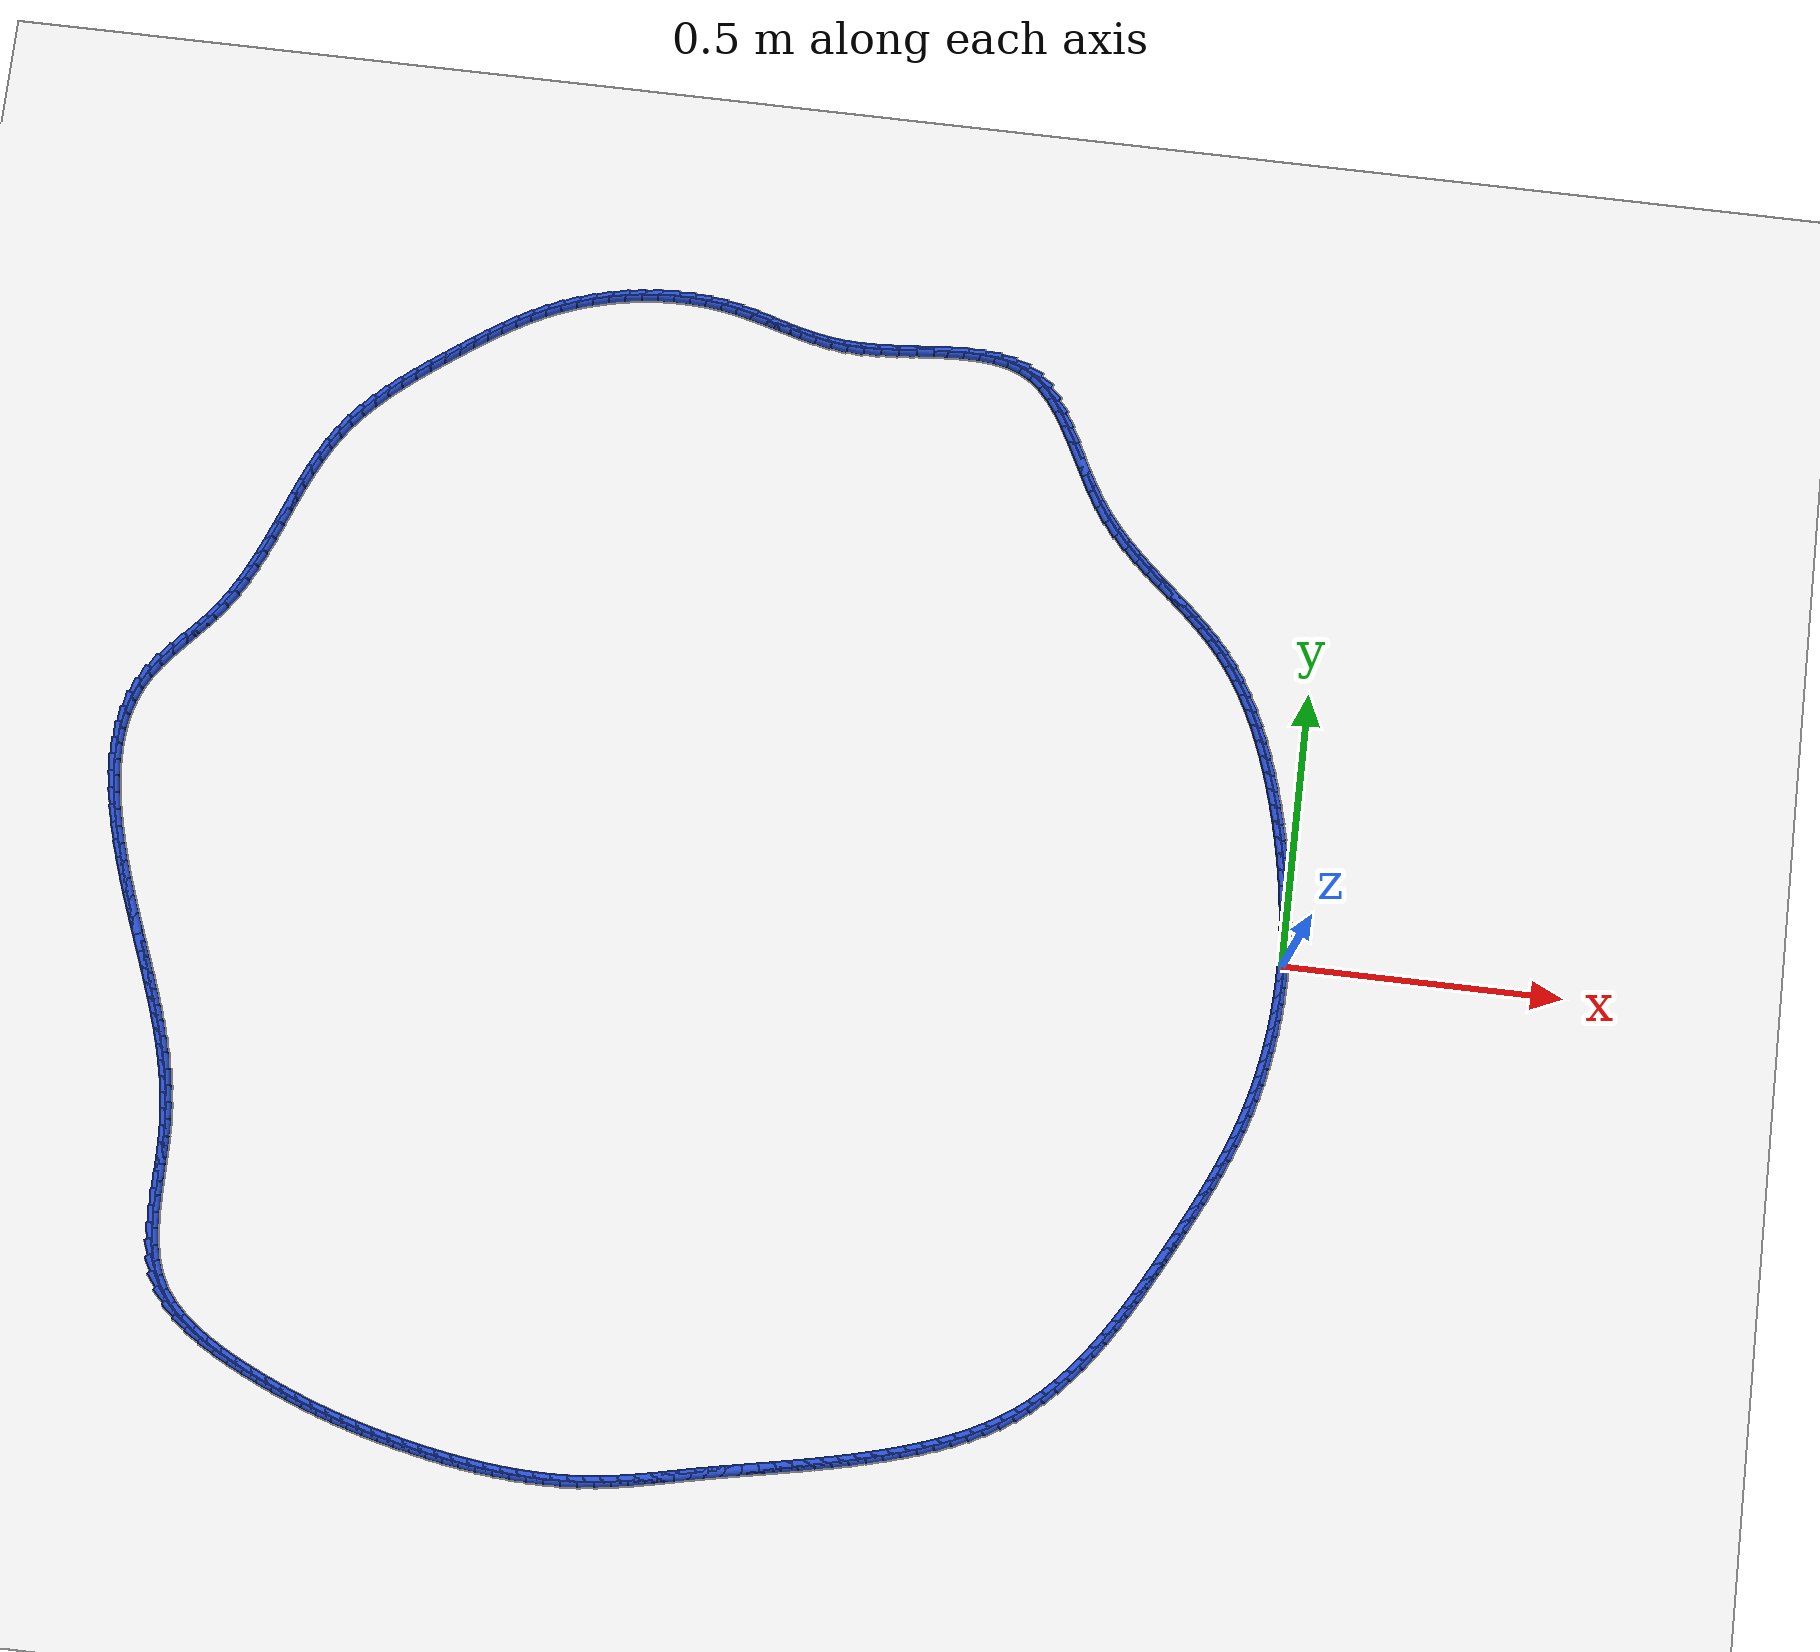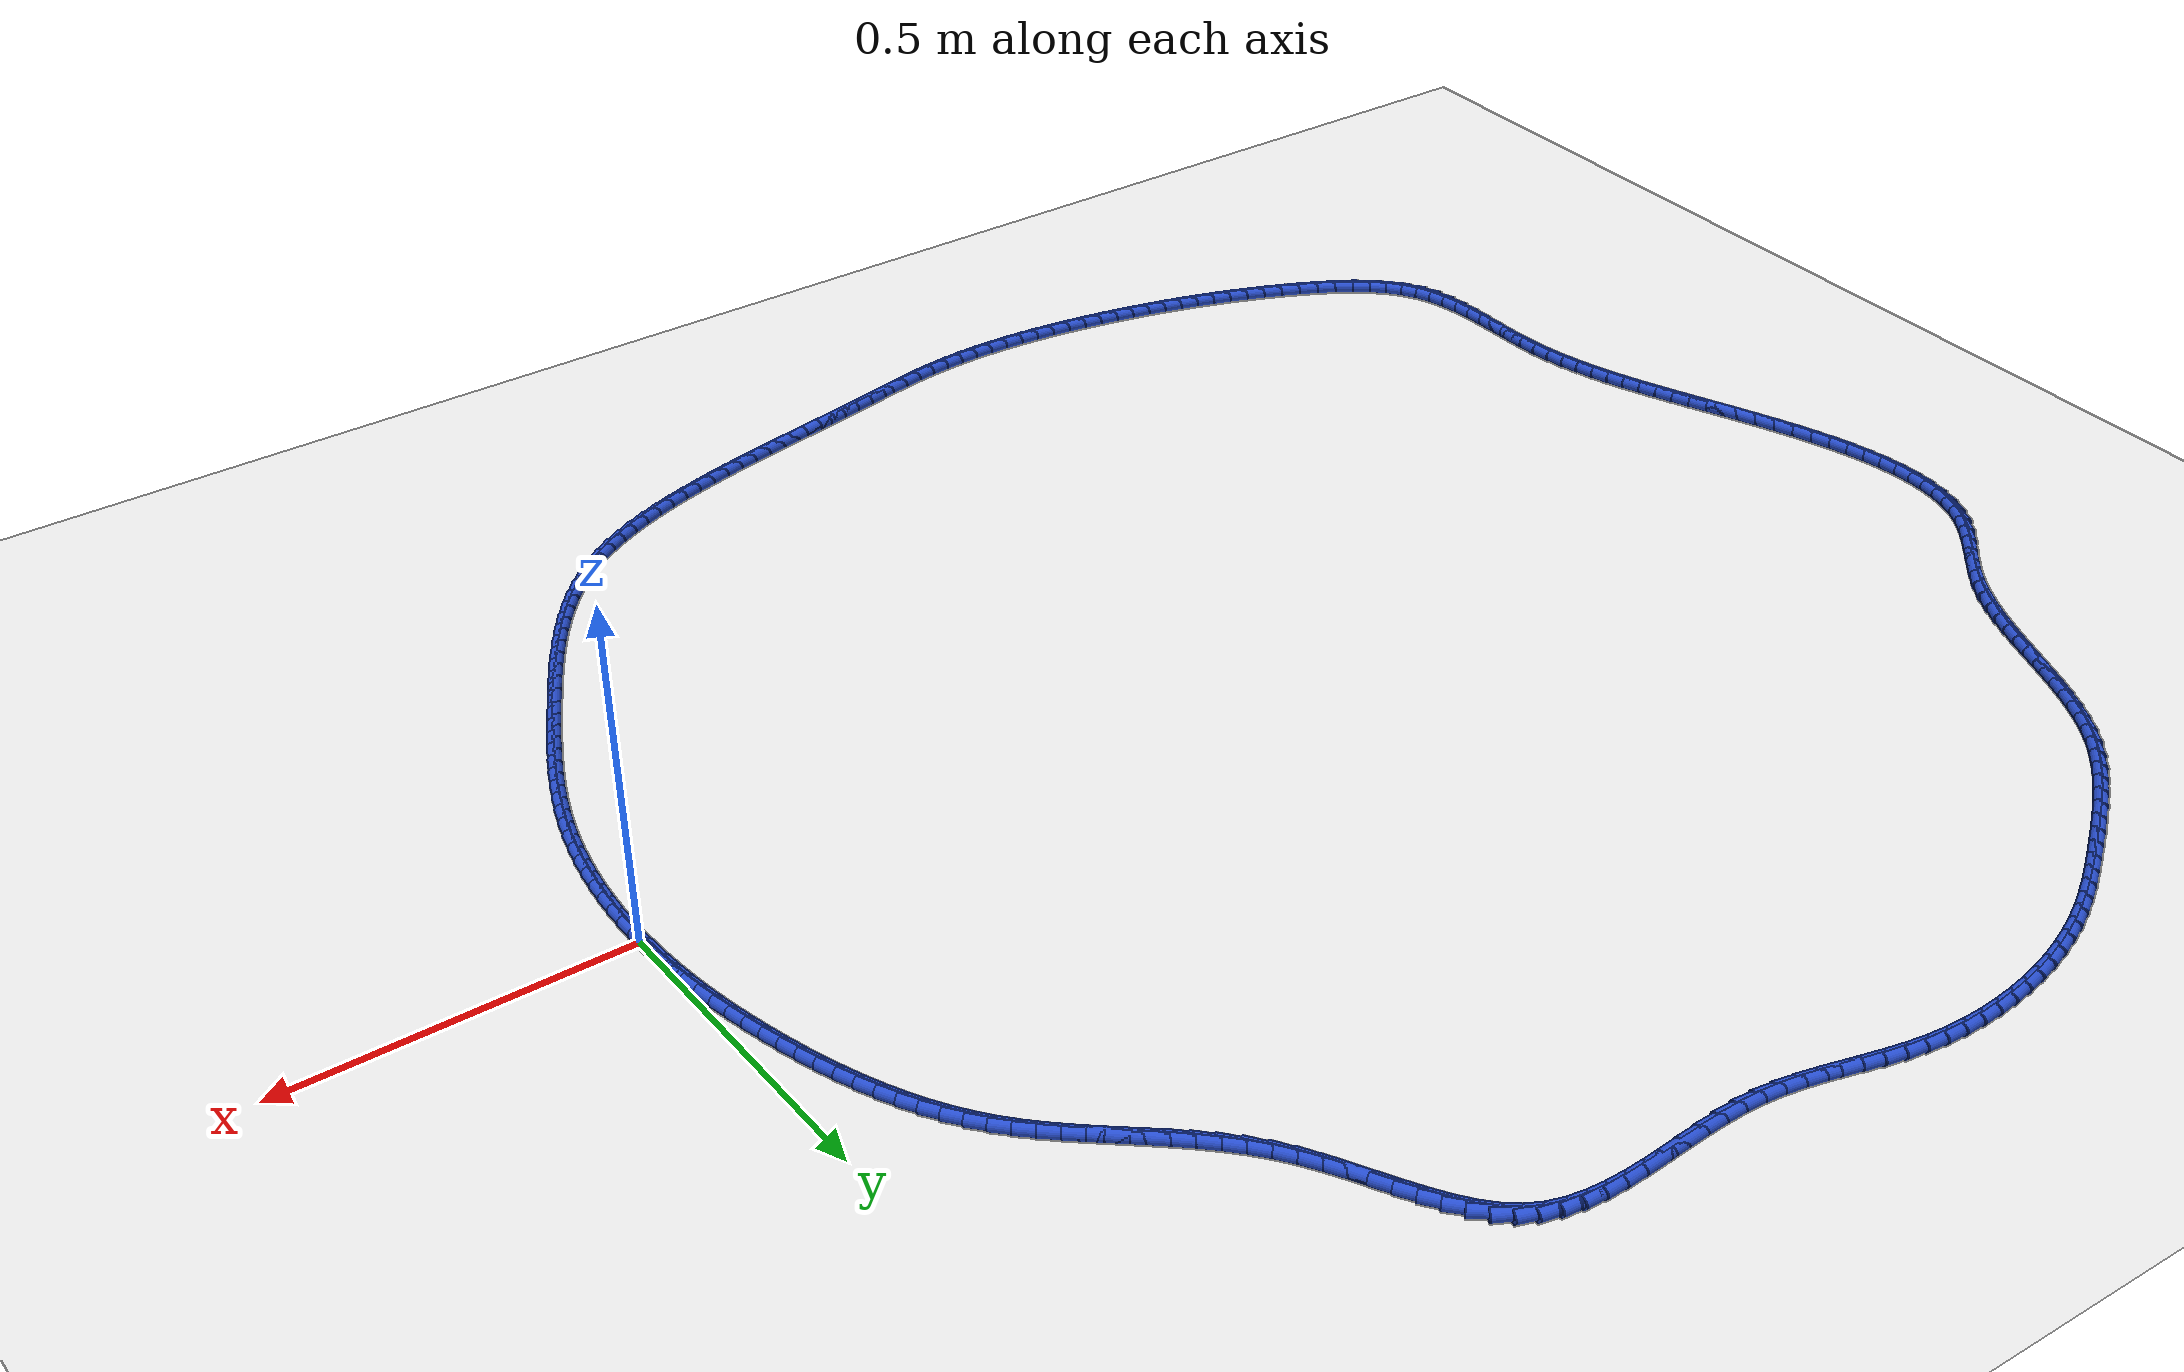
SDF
<sdf version="1.6">
 <world name="default">
  <light name="sun" type="directional">
   <pose>0 0 10 0 -0 0</pose>
   <diffuse>0.8 0.8 0.8 1</diffuse>
   <specular>0.2 0.2 0.2 1</specular>
   <attenuation>
    <range>1000</range>
    <constant>0.9</constant>
    <linear>0.01</linear>
    <quadratic>0.001</quadratic>
   </attenuation>
   <direction>-0.5 0.1 -0.9</direction>
  </light>
  <model name="ground_plane">
   <static>1</static>
   <link name="link">
    <collision name="collision">
     <geometry><plane><normal>0 0 1</normal><size>100 100</size></plane></geometry>
     <surface><friction><ode><mu>100</mu><mu2>50</mu2></ode></friction></surface>
    </collision>
    <visual name="visual">
     <cast_shadows>0</cast_shadows>
     <geometry><plane><normal>0 0 1</normal><size>100 100</size></plane></geometry>
     <material>
      <script><uri>file://media/materials/scripts/gazebo.material</uri><name>Gazebo/WhiteGlow</name></script>
     </material>
    </visual>
   </link>
  </model>
  <gravity>0 0 -9.8</gravity>
  <magnetic_field>6e-06 2.3e-05 -4.2e-05</magnetic_field>
  <atmosphere type="adiabatic"/>
  <physics name="default_physics" default="0" type="ode">
   <max_step_size>0.001</max_step_size>
   <real_time_factor>1</real_time_factor>
   <real_time_update_rate>1000</real_time_update_rate>
  </physics>
  <scene><ambient>0.4 0.4 0.4 1</ambient><background>0.7 0.7 0.7 1</background><shadows>1</shadows></scene>
  <spherical_coordinates>
   <surface_model>EARTH_WGS84</surface_model>
   <latitude_deg>0</latitude_deg>
   <longitude_deg>0</longitude_deg>
   <elevation>0</elevation>
   <heading_deg>0</heading_deg>
  </spherical_coordinates>
  <model name="line">
   <link name="link_0">
    <pose>-3.469446951953614e-18 -4.163336342344337e-17 0.01 0 1.57 -1.5466826521365722</pose>
    <collision name="collision">
     <geometry><cylinder><radius>0.01</radius><length>0.08</length></cylinder></geometry>
    </collision>
    <visual name="visual">
     <material>
      <script><name>Gazebo/Blue</name><uri>file://media/materials/scripts/gazebo.material</uri></script>
     </material>
     <geometry><cylinder><radius>0.01</radius><length>0.08</length></cylinder></geometry>
    </visual>
   </link>
   <link name="link_1">
    <pose>-0.0007096333509930941 0.029422964868558183 0.01 0 1.57 -1.5170776853234302</pose>
    <collision name="collision">
     <geometry><cylinder><radius>0.01</radius><length>0.08</length></cylinder></geometry>
    </collision>
    <visual name="visual">
     <material>
      <script><name>Gazebo/Blue</name><uri>file://media/materials/scripts/gazebo.material</uri></script>
     </material>
     <geometry><cylinder><radius>0.01</radius><length>0.08</length></cylinder></geometry>
    </visual>
   </link>
   <link name="link_2">
    <pose>-0.0022868037492940483 0.05875455232076186 0.01 0 1.57 -1.4883658231498254</pose>
    <collision name="collision">
     <geometry><cylinder><radius>0.01</radius><length>0.08</length></cylinder></geometry>
    </collision>
    <visual name="visual">
     <material>
      <script><name>Gazebo/Blue</name><uri>file://media/materials/scripts/gazebo.material</uri></script>
     </material>
     <geometry><cylinder><radius>0.01</radius><length>0.08</length></cylinder></geometry>
    </visual>
   </link>
   <link name="link_3">
    <pose>-0.004703602148593343 0.08800734023232486 0.01 0 1.57 -1.4606276589522176</pose>
    <collision name="collision">
     <geometry><cylinder><radius>0.01</radius><length>0.08</length></cylinder></geometry>
    </collision>
    <visual name="visual">
     <material>
      <script><name>Gazebo/Blue</name><uri>file://media/materials/scripts/gazebo.material</uri></script>
     </material>
     <geometry><cylinder><radius>0.01</radius><length>0.08</length></cylinder></geometry>
    </visual>
   </link>
   <link name="link_4">
    <pose>-0.00793211950258145 0.11719390647896095 0.01 0 1.57 -1.4339324970044878</pose>
    <collision name="collision">
     <geometry><cylinder><radius>0.01</radius><length>0.08</length></cylinder></geometry>
    </collision>
    <visual name="visual">
     <material>
      <script><name>Gazebo/Blue</name><uri>file://media/materials/scripts/gazebo.material</uri></script>
     </material>
     <geometry><cylinder><radius>0.01</radius><length>0.08</length></cylinder></geometry>
    </visual>
   </link>
   <link name="link_5">
    <pose>-0.011944446764948845 0.14632682893638393 0.01 0 1.57 -1.4083383048291738</pose>
    <collision name="collision">
     <geometry><cylinder><radius>0.01</radius><length>0.08</length></cylinder></geometry>
    </collision>
    <visual name="visual">
     <material>
      <script><name>Gazebo/Blue</name><uri>file://media/materials/scripts/gazebo.material</uri></script>
     </material>
     <geometry><cylinder><radius>0.01</radius><length>0.08</length></cylinder></geometry>
    </visual>
   </link>
   <link name="link_6">
    <pose>-0.016712674889385996 0.17541868548030773 0.01 0 1.57 -1.3838919719361213</pose>
    <collision name="collision">
     <geometry><cylinder><radius>0.01</radius><length>0.08</length></cylinder></geometry>
    </collision>
    <visual name="visual">
     <material>
      <script><name>Gazebo/Blue</name><uri>file://media/materials/scripts/gazebo.material</uri></script>
     </material>
     <geometry><cylinder><radius>0.01</radius><length>0.08</length></cylinder></geometry>
    </visual>
   </link>
   <link name="link_7">
    <pose>-0.02220889482958338 0.20448205398644603 0.01 0 1.57 -1.3606298222673068</pose>
    <collision name="collision">
     <geometry><cylinder><radius>0.01</radius><length>0.08</length></cylinder></geometry>
    </collision>
    <visual name="visual">
     <material>
      <script><name>Gazebo/Blue</name><uri>file://media/materials/scripts/gazebo.material</uri></script>
     </material>
     <geometry><cylinder><radius>0.01</radius><length>0.08</length></cylinder></geometry>
    </visual>
   </link>
   <link name="link_8">
    <pose>-0.028405197539231476 0.23352951233051272 0.01 0 1.57 -1.3385783231318669</pose>
    <collision name="collision">
     <geometry><cylinder><radius>0.01</radius><length>0.08</length></cylinder></geometry>
    </collision>
    <visual name="visual">
     <material>
      <script><name>Gazebo/Blue</name><uri>file://media/materials/scripts/gazebo.material</uri></script>
     </material>
     <geometry><cylinder><radius>0.01</radius><length>0.08</length></cylinder></geometry>
    </visual>
   </link>
   <link name="link_9">
    <pose>-0.03527367397202075 0.26257363838822156 0.01 0 1.57 -1.317455571323649</pose>
    <collision name="collision">
     <geometry><cylinder><radius>0.01</radius><length>0.08</length></cylinder></geometry>
    </collision>
    <visual name="visual">
     <material>
      <script><name>Gazebo/Blue</name><uri>file://media/materials/scripts/gazebo.material</uri></script>
     </material>
     <geometry><cylinder><radius>0.01</radius><length>0.08</length></cylinder></geometry>
    </visual>
   </link>
   <link name="link_10">
    <pose>-0.04279330992532219 0.29161779840882757 0.01 0 1.57 -1.2946354571706151</pose>
    <collision name="collision">
     <geometry><cylinder><radius>0.01</radius><length>0.08</length></cylinder></geometry>
    </collision>
    <visual name="visual">
     <material>
      <script><name>Gazebo/Blue</name><uri>file://media/materials/scripts/gazebo.material</uri></script>
     </material>
     <geometry><cylinder><radius>0.01</radius><length>0.08</length></cylinder></geometry>
    </visual>
   </link>
   <link name="link_11">
    <pose>-0.05100283485617517 0.32058554011318197 0.01 0 1.57 -1.2686417127740708</pose>
    <collision name="collision">
     <geometry><cylinder><radius>0.01</radius><length>0.08</length></cylinder></geometry>
    </collision>
    <visual name="visual">
     <material>
      <script><name>Gazebo/Blue</name><uri>file://media/materials/scripts/gazebo.material</uri></script>
     </material>
     <geometry><cylinder><radius>0.01</radius><length>0.08</length></cylinder></geometry>
    </visual>
   </link>
   <link name="link_12">
    <pose>-0.059971627032978723 0.34935946389762257 0.01 0 1.57 -1.2392683616072475</pose>
    <collision name="collision">
     <geometry><cylinder><radius>0.01</radius><length>0.08</length></cylinder></geometry>
    </collision>
    <visual name="visual">
     <material>
      <script><name>Gazebo/Blue</name><uri>file://media/materials/scripts/gazebo.material</uri></script>
     </material>
     <geometry><cylinder><radius>0.01</radius><length>0.08</length></cylinder></geometry>
    </visual>
   </link>
   <link name="link_13">
    <pose>-0.06976931467259165 0.37782183622316506 0.01 0 1.57 -1.206289774604742</pose>
    <collision name="collision">
     <geometry><cylinder><radius>0.01</radius><length>0.08</length></cylinder></geometry>
    </collision>
    <visual name="visual">
     <material>
      <script><name>Gazebo/Blue</name><uri>file://media/materials/scripts/gazebo.material</uri></script>
     </material>
     <geometry><cylinder><radius>0.01</radius><length>0.08</length></cylinder></geometry>
    </visual>
   </link>
   <link name="link_14">
    <pose>-0.08046552599187284 0.4058549235508256 0.01 0 1.57 -1.169456326770395</pose>
    <collision name="collision">
     <geometry><cylinder><radius>0.01</radius><length>0.08</length></cylinder></geometry>
    </collision>
    <visual name="visual">
     <material>
      <script><name>Gazebo/Blue</name><uri>file://media/materials/scripts/gazebo.material</uri></script>
     </material>
     <geometry><cylinder><radius>0.01</radius><length>0.08</length></cylinder></geometry>
    </visual>
   </link>
   <link name="link_15">
    <pose>-0.0921298892076811 0.4333409923416196 0.01 0 1.57 -1.12850404834102</pose>
    <collision name="collision">
     <geometry><cylinder><radius>0.01</radius><length>0.08</length></cylinder></geometry>
    </collision>
    <visual name="visual">
     <material>
      <script><name>Gazebo/Blue</name><uri>file://media/materials/scripts/gazebo.material</uri></script>
     </material>
     <geometry><cylinder><radius>0.01</radius><length>0.08</length></cylinder></geometry>
    </visual>
   </link>
   <link name="link_16">
    <pose>-0.10483203253687526 0.4601623090565631 0.01 0 1.57 -1.0831688101588135</pose>
    <collision name="collision">
     <geometry><cylinder><radius>0.01</radius><length>0.08</length></cylinder></geometry>
    </collision>
    <visual name="visual">
     <material>
      <script><name>Gazebo/Blue</name><uri>file://media/materials/scripts/gazebo.material</uri></script>
     </material>
     <geometry><cylinder><radius>0.01</radius><length>0.08</length></cylinder></geometry>
    </visual>
   </link>
   <link name="link_17">
    <pose>-0.11864158419631418 0.48620114015667176 0.01 0 1.57 -1.0332065102352515</pose>
    <collision name="collision">
     <geometry><cylinder><radius>0.01</radius><length>0.08</length></cylinder></geometry>
    </collision>
    <visual name="visual">
     <material>
      <script><name>Gazebo/Blue</name><uri>file://media/materials/scripts/gazebo.material</uri></script>
     </material>
     <geometry><cylinder><radius>0.01</radius><length>0.08</length></cylinder></geometry>
    </visual>
   </link>
   <link name="link_18">
    <pose>-0.13362817240285668 0.5113397521029615 0.01 0 1.57 -0.9784205083939612</pose>
    <collision name="collision">
     <geometry><cylinder><radius>0.01</radius><length>0.08</length></cylinder></geometry>
    </collision>
    <visual name="visual">
     <material>
      <script><name>Gazebo/Blue</name><uri>file://media/materials/scripts/gazebo.material</uri></script>
     </material>
     <geometry><cylinder><radius>0.01</radius><length>0.08</length></cylinder></geometry>
    </visual>
   </link>
   <link name="link_19">
    <pose>-0.14986142537336156 0.5354604113564478 0.01 0 1.57 -0.9186967897504351</pose>
    <collision name="collision">
     <geometry><cylinder><radius>0.01</radius><length>0.08</length></cylinder></geometry>
    </collision>
    <visual name="visual">
     <material>
      <script><name>Gazebo/Blue</name><uri>file://media/materials/scripts/gazebo.material</uri></script>
     </material>
     <geometry><cylinder><radius>0.01</radius><length>0.08</length></cylinder></geometry>
    </visual>
   </link>
   <link name="link_20">
    <pose>-0.16741097132468777 0.558445384378147 0.01 0 1.57 -0.8562782998868227</pose>
    <collision name="collision">
     <geometry><cylinder><radius>0.01</radius><length>0.08</length></cylinder></geometry>
    </collision>
    <visual name="visual">
     <material>
      <script><name>Gazebo/Blue</name><uri>file://media/materials/scripts/gazebo.material</uri></script>
     </material>
     <geometry><cylinder><radius>0.01</radius><length>0.08</length></cylinder></geometry>
    </visual>
   </link>
   <link name="link_21">
    <pose>-0.18630445428821077 0.5802267435483839 0.01 0 1.57 -0.802872218110293</pose>
    <collision name="collision">
     <geometry><cylinder><radius>0.01</radius><length>0.08</length></cylinder></geometry>
    </collision>
    <visual name="visual">
     <material>
      <script><name>Gazebo/Blue</name><uri>file://media/materials/scripts/gazebo.material</uri></script>
     </material>
     <geometry><cylinder><radius>0.01</radius><length>0.08</length></cylinder></geometry>
    </visual>
   </link>
   <link name="link_22">
    <pose>-0.20635522078494595 0.6009907827927262 0.01 0 1.57 -0.7624744068336484</pose>
    <collision name="collision">
     <geometry><cylinder><radius>0.01</radius><length>0.08</length></cylinder></geometry>
    </collision>
    <visual name="visual">
     <material>
      <script><name>Gazebo/Blue</name><uri>file://media/materials/scripts/gazebo.material</uri></script>
     </material>
     <geometry><cylinder><radius>0.01</radius><length>0.08</length></cylinder></geometry>
    </visual>
   </link>
   <link name="link_23">
    <pose>-0.22730842062482756 0.6210046979251593 0.01 0 1.57 -0.7351209951692624</pose>
    <collision name="collision">
     <geometry><cylinder><radius>0.01</radius><length>0.08</length></cylinder></geometry>
    </collision>
    <visual name="visual">
     <material>
      <script><name>Gazebo/Blue</name><uri>file://media/materials/scripts/gazebo.material</uri></script>
     </material>
     <geometry><cylinder><radius>0.01</radius><length>0.08</length></cylinder></geometry>
    </visual>
   </link>
   <link name="link_24">
    <pose>-0.24890917492477538 0.6405357187982464 0.01 0 1.57 -0.7206581626860784</pose>
    <collision name="collision">
     <geometry><cylinder><radius>0.01</radius><length>0.08</length></cylinder></geometry>
    </collision>
    <visual name="visual">
     <material>
      <script><name>Gazebo/Blue</name><uri>file://media/materials/scripts/gazebo.material</uri></script>
     </material>
     <geometry><cylinder><radius>0.01</radius><length>0.08</length></cylinder></geometry>
    </visual>
   </link>
   <link name="link_25">
    <pose>-0.27090260480170913 0.6598510752645507 0.01 0 1.57 -0.718883705059251</pose>
    <collision name="collision">
     <geometry><cylinder><radius>0.01</radius><length>0.08</length></cylinder></geometry>
    </collision>
    <visual name="visual">
     <material>
      <script><name>Gazebo/Blue</name><uri>file://media/materials/scripts/gazebo.material</uri></script>
     </material>
     <geometry><cylinder><radius>0.01</radius><length>0.08</length></cylinder></geometry>
    </visual>
   </link>
   <link name="link_26">
    <pose>-0.2930338313725486 0.6792179971766351 0.01 0 1.57 -0.7296183190790568</pose>
    <collision name="collision">
     <geometry><cylinder><radius>0.01</radius><length>0.08</length></cylinder></geometry>
    </collision>
    <visual name="visual">
     <material>
      <script><name>Gazebo/Blue</name><uri>file://media/materials/scripts/gazebo.material</uri></script>
     </material>
     <geometry><cylinder><radius>0.01</radius><length>0.08</length></cylinder></geometry>
    </visual>
   </link>
   <link name="link_27">
    <pose>-0.31504797575421356 0.6989037143870633 0.01 0 1.57 -0.7527132531716278</pose>
    <collision name="collision">
     <geometry><cylinder><radius>0.01</radius><length>0.08</length></cylinder></geometry>
    </collision>
    <visual name="visual">
     <material>
      <script><name>Gazebo/Blue</name><uri>file://media/materials/scripts/gazebo.material</uri></script>
     </material>
     <geometry><cylinder><radius>0.01</radius><length>0.08</length></cylinder></geometry>
    </visual>
   </link>
   <link name="link_28">
    <pose>-0.33669015906362393 0.7191754567483987 0.01 0 1.57 -0.7880002724779869</pose>
    <collision name="collision">
     <geometry><cylinder><radius>0.01</radius><length>0.08</length></cylinder></geometry>
    </collision>
    <visual name="visual">
     <material>
      <script><name>Gazebo/Blue</name><uri>file://media/materials/scripts/gazebo.material</uri></script>
     </material>
     <geometry><cylinder><radius>0.01</radius><length>0.08</length></cylinder></geometry>
    </visual>
   </link>
   <link name="link_29">
    <pose>-0.3577055024176993 0.7403004541132038 0.01 0 1.57 -0.8351894958791275</pose>
    <collision name="collision">
     <geometry><cylinder><radius>0.01</radius><length>0.08</length></cylinder></geometry>
    </collision>
    <visual name="visual">
     <material>
      <script><name>Gazebo/Blue</name><uri>file://media/materials/scripts/gazebo.material</uri></script>
     </material>
     <geometry><cylinder><radius>0.01</radius><length>0.08</length></cylinder></geometry>
    </visual>
   </link>
   <link name="link_30">
    <pose>-0.37783912693335936 0.7625459363340423 0.01 0 1.57 -0.8937255576262926</pose>
    <collision name="collision">
     <geometry><cylinder><radius>0.01</radius><length>0.08</length></cylinder></geometry>
    </collision>
    <visual name="visual">
     <material>
      <script><name>Gazebo/Blue</name><uri>file://media/materials/scripts/gazebo.material</uri></script>
     </material>
     <geometry><cylinder><radius>0.01</radius><length>0.08</length></cylinder></geometry>
    </visual>
   </link>
   <link name="link_31">
    <pose>-0.3968361537275239 0.7861791332634773 0.01 0 1.57 -0.9624294779526396</pose>
    <collision name="collision">
     <geometry><cylinder><radius>0.01</radius><length>0.08</length></cylinder></geometry>
    </collision>
    <visual name="visual">
     <material>
      <script><name>Gazebo/Blue</name><uri>file://media/materials/scripts/gazebo.material</uri></script>
     </material>
     <geometry><cylinder><radius>0.01</radius><length>0.08</length></cylinder></geometry>
    </visual>
   </link>
   <link name="link_32">
    <pose>-0.4144455172038463 0.8114621173892622 0.01 0 1.57 -1.0276484594299946</pose>
    <collision name="collision">
     <geometry><cylinder><radius>0.01</radius><length>0.08</length></cylinder></geometry>
    </collision>
    <visual name="visual">
     <material>
      <script><name>Gazebo/Blue</name><uri>file://media/materials/scripts/gazebo.material</uri></script>
     </material>
     <geometry><cylinder><radius>0.01</radius><length>0.08</length></cylinder></geometry>
    </visual>
   </link>
   <link name="link_33">
    <pose>-0.4306624185271714 0.8383238922177547 0.01 0 1.57 -1.070710505359135</pose>
    <collision name="collision">
     <geometry><cylinder><radius>0.01</radius><length>0.08</length></cylinder></geometry>
    </collision>
    <visual name="visual">
     <material>
      <script><name>Gazebo/Blue</name><uri>file://media/materials/scripts/gazebo.material</uri></script>
     </material>
     <geometry><cylinder><radius>0.01</radius><length>0.08</length></cylinder></geometry>
    </visual>
   </link>
   <link name="link_34">
    <pose>-0.44587417131279616 0.8661631400141048 0.01 0 1.57 -1.0917946703447043</pose>
    <collision name="collision">
     <geometry><cylinder><radius>0.01</radius><length>0.08</length></cylinder></geometry>
    </collision>
    <visual name="visual">
     <material>
      <script><name>Gazebo/Blue</name><uri>file://media/materials/scripts/gazebo.material</uri></script>
     </material>
     <geometry><cylinder><radius>0.01</radius><length>0.08</length></cylinder></geometry>
    </visual>
   </link>
   <link name="link_35">
    <pose>-0.460503064657572 0.8943312396722747 0.01 0 1.57 -1.0916391535742775</pose>
    <collision name="collision">
     <geometry><cylinder><radius>0.01</radius><length>0.08</length></cylinder></geometry>
    </collision>
    <visual name="visual">
     <material>
      <script><name>Gazebo/Blue</name><uri>file://media/materials/scripts/gazebo.material</uri></script>
     </material>
     <geometry><cylinder><radius>0.01</radius><length>0.08</length></cylinder></geometry>
    </visual>
   </link>
   <link name="link_36">
    <pose>-0.47497138765835084 0.9221795700862281 0.01 0 1.57 -1.0694946534134544</pose>
    <collision name="collision">
     <geometry><cylinder><radius>0.01</radius><length>0.08</length></cylinder></geometry>
    </collision>
    <visual name="visual">
     <material>
      <script><name>Gazebo/Blue</name><uri>file://media/materials/scripts/gazebo.material</uri></script>
     </material>
     <geometry><cylinder><radius>0.01</radius><length>0.08</length></cylinder></geometry>
    </visual>
   </link>
   <link name="link_37">
    <pose>-0.48970142941198425 0.949059510149928 0.01 0 1.57 -1.0229506416498728</pose>
    <collision name="collision">
     <geometry><cylinder><radius>0.01</radius><length>0.08</length></cylinder></geometry>
    </collision>
    <visual name="visual">
     <material>
      <script><name>Gazebo/Blue</name><uri>file://media/materials/scripts/gazebo.material</uri></script>
     </material>
     <geometry><cylinder><radius>0.01</radius><length>0.08</length></cylinder></geometry>
    </visual>
   </link>
   <link name="link_38">
    <pose>-0.5051154790153239 0.9743224387573374 0.01 0 1.57 -0.9478539412121977</pose>
    <collision name="collision">
     <geometry><cylinder><radius>0.01</radius><length>0.08</length></cylinder></geometry>
    </collision>
    <visual name="visual">
     <material>
      <script><name>Gazebo/Blue</name><uri>file://media/materials/scripts/gazebo.material</uri></script>
     </material>
     <geometry><cylinder><radius>0.01</radius><length>0.08</length></cylinder></geometry>
    </visual>
   </link>
   <link name="link_39">
    <pose>-0.5216358255652217 0.9973197348024196 0.01 0 1.57 -0.8386915914948528</pose>
    <collision name="collision">
     <geometry><cylinder><radius>0.01</radius><length>0.08</length></cylinder></geometry>
    </collision>
    <visual name="visual">
     <material>
      <script><name>Gazebo/Blue</name><uri>file://media/materials/scripts/gazebo.material</uri></script>
     </material>
     <geometry><cylinder><radius>0.01</radius><length>0.08</length></cylinder></geometry>
    </visual>
   </link>
   <link name="link_40">
    <pose>-0.5396847581585293 1.017402777179138 0.01 0 1.57 -0.6904044710407707</pose>
    <collision name="collision">
     <geometry><cylinder><radius>0.01</radius><length>0.08</length></cylinder></geometry>
    </collision>
    <visual name="visual">
     <material>
      <script><name>Gazebo/Blue</name><uri>file://media/materials/scripts/gazebo.material</uri></script>
     </material>
     <geometry><cylinder><radius>0.01</radius><length>0.08</length></cylinder></geometry>
    </visual>
   </link>
   <link name="link_41">
    <pose>-0.5596845658920985 1.0339229447814557 0.01 0 1.57 -0.5077230441998889</pose>
    <collision name="collision">
     <geometry><cylinder><radius>0.01</radius><length>0.08</length></cylinder></geometry>
    </collision>
    <visual name="visual">
     <material>
      <script><name>Gazebo/Blue</name><uri>file://media/materials/scripts/gazebo.material</uri></script>
     </material>
     <geometry><cylinder><radius>0.01</radius><length>0.08</length></cylinder></geometry>
    </visual>
   </link>
   <link name="link_42">
    <pose>-0.5819964599935963 1.0463366833250862 0.01 0 1.57 -0.33475441965120206</pose>
    <collision name="collision">
     <geometry><cylinder><radius>0.01</radius><length>0.08</length></cylinder></geometry>
    </collision>
    <visual name="visual">
     <material>
      <script><name>Gazebo/Blue</name><uri>file://media/materials/scripts/gazebo.material</uri></script>
     </material>
     <geometry><cylinder><radius>0.01</radius><length>0.08</length></cylinder></geometry>
    </visual>
   </link>
   <link name="link_43">
    <pose>-0.6065332893854085 1.0548717162903005 0.01 0 1.57 -0.19495138236947562</pose>
    <collision name="collision">
     <geometry><cylinder><radius>0.01</radius><length>0.08</length></cylinder></geometry>
    </collision>
    <visual name="visual">
     <material>
      <script><name>Gazebo/Blue</name><uri>file://media/materials/scripts/gazebo.material</uri></script>
     </material>
     <geometry><cylinder><radius>0.01</radius><length>0.08</length></cylinder></geometry>
    </visual>
   </link>
   <link name="link_44">
    <pose>-0.6330081296176658 1.0600994195076165 0.01 0 1.57 -0.08842044995669045</pose>
    <collision name="collision">
     <geometry><cylinder><radius>0.01</radius><length>0.08</length></cylinder></geometry>
    </collision>
    <visual name="visual">
     <material>
      <script><name>Gazebo/Blue</name><uri>file://media/materials/scripts/gazebo.material</uri></script>
     </material>
     <geometry><cylinder><radius>0.01</radius><length>0.08</length></cylinder></geometry>
    </visual>
   </link>
   <link name="link_45">
    <pose>-0.6611331390091282 1.0625927466390317 0.01 0 1.57 -0.011255363388057046</pose>
    <collision name="collision">
     <geometry><cylinder><radius>0.01</radius><length>0.08</length></cylinder></geometry>
    </collision>
    <visual name="visual">
     <material>
      <script><name>Gazebo/Blue</name><uri>file://media/materials/scripts/gazebo.material</uri></script>
     </material>
     <geometry><cylinder><radius>0.01</radius><length>0.08</length></cylinder></geometry>
    </visual>
   </link>
   <link name="link_46">
    <pose>-0.6906204758785567 1.0629246513465456 0.01 0 1.57 0.041092336631190975</pose>
    <collision name="collision">
     <geometry><cylinder><radius>0.01</radius><length>0.08</length></cylinder></geometry>
    </collision>
    <visual name="visual">
     <material>
      <script><name>Gazebo/Blue</name><uri>file://media/materials/scripts/gazebo.material</uri></script>
     </material>
     <geometry><cylinder><radius>0.01</radius><length>0.08</length></cylinder></geometry>
    </visual>
   </link>
   <link name="link_47">
    <pose>-0.7211822985447117 1.0616680872921556 0.01 0 1.57 0.0723516460611456</pose>
    <collision name="collision">
     <geometry><cylinder><radius>0.01</radius><length>0.08</length></cylinder></geometry>
    </collision>
    <visual name="visual">
     <material>
      <script><name>Gazebo/Blue</name><uri>file://media/materials/scripts/gazebo.material</uri></script>
     </material>
     <geometry><cylinder><radius>0.01</radius><length>0.08</length></cylinder></geometry>
    </visual>
   </link>
   <link name="link_48">
    <pose>-0.7525307653263539 1.0593960081378606 0.01 0 1.57 0.08503380484491192</pose>
    <collision name="collision">
     <geometry><cylinder><radius>0.01</radius><length>0.08</length></cylinder></geometry>
    </collision>
    <visual name="visual">
     <material>
      <script><name>Gazebo/Blue</name><uri>file://media/materials/scripts/gazebo.material</uri></script>
     </material>
     <geometry><cylinder><radius>0.01</radius><length>0.08</length></cylinder></geometry>
    </visual>
   </link>
   <link name="link_49">
    <pose>-0.7843780345422435 1.0566813675456592 0.01 0 1.57 0.08043714475463372</pose>
    <collision name="collision">
     <geometry><cylinder><radius>0.01</radius><length>0.08</length></cylinder></geometry>
    </collision>
    <visual name="visual">
     <material>
      <script><name>Gazebo/Blue</name><uri>file://media/materials/scripts/gazebo.material</uri></script>
     </material>
     <geometry><cylinder><radius>0.01</radius><length>0.08</length></cylinder></geometry>
    </visual>
   </link>
   <link name="link_50">
    <pose>-0.816436264511142 1.0540971191775501 0.01 0 1.57 0.058744812370201585</pose>
    <collision name="collision">
     <geometry><cylinder><radius>0.01</radius><length>0.08</length></cylinder></geometry>
    </collision>
    <visual name="visual">
     <material>
      <script><name>Gazebo/Blue</name><uri>file://media/materials/scripts/gazebo.material</uri></script>
     </material>
     <geometry><cylinder><radius>0.01</radius><length>0.08</length></cylinder></geometry>
    </visual>
   </link>
   <link name="link_51">
    <pose>-0.8484176135518091 1.052216216695531 0.01 0 1.57 0.019120612154705993</pose>
    <collision name="collision">
     <geometry><cylinder><radius>0.01</radius><length>0.08</length></cylinder></geometry>
    </collision>
    <visual name="visual">
     <material>
      <script><name>Gazebo/Blue</name><uri>file://media/materials/scripts/gazebo.material</uri></script>
     </material>
     <geometry><cylinder><radius>0.01</radius><length>0.08</length></cylinder></geometry>
    </visual>
   </link>
   <link name="link_52">
    <pose>-0.880034239983006 1.0516116137616012 0.01 0 1.57 -0.04017497977391452</pose>
    <collision name="collision">
     <geometry><cylinder><radius>0.01</radius><length>0.08</length></cylinder></geometry>
    </collision>
    <visual name="visual">
     <material>
      <script><name>Gazebo/Blue</name><uri>file://media/materials/scripts/gazebo.material</uri></script>
     </material>
     <geometry><cylinder><radius>0.01</radius><length>0.08</length></cylinder></geometry>
    </visual>
   </link>
   <link name="link_53">
    <pose>-0.9109983021234928 1.0528562640377586 0.01 0 1.57 -0.11595838396832246</pose>
    <collision name="collision">
     <geometry><cylinder><radius>0.01</radius><length>0.08</length></cylinder></geometry>
    </collision>
    <visual name="visual">
     <material>
      <script><name>Gazebo/Blue</name><uri>file://media/materials/scripts/gazebo.material</uri></script>
     </material>
     <geometry><cylinder><radius>0.01</radius><length>0.08</length></cylinder></geometry>
    </visual>
   </link>
   <link name="link_54">
    <pose>-0.9410908269717277 1.0563614694259793 0.01 0 1.57 -0.1829352062556781</pose>
    <collision name="collision">
     <geometry><cylinder><radius>0.01</radius><length>0.08</length></cylinder></geometry>
    </collision>
    <visual name="visual">
     <material>
      <script><name>Gazebo/Blue</name><uri>file://media/materials/scripts/gazebo.material</uri></script>
     </material>
     <geometry><cylinder><radius>0.01</radius><length>0.08</length></cylinder></geometry>
    </visual>
   </link>
   <link name="link_55">
    <pose>-0.9704133416913429 1.0617862389715136 0.01 0 1.57 -0.23177026849941898</pose>
    <collision name="collision">
     <geometry><cylinder><radius>0.01</radius><length>0.08</length></cylinder></geometry>
    </collision>
    <visual name="visual">
     <material>
      <script><name>Gazebo/Blue</name><uri>file://media/materials/scripts/gazebo.material</uri></script>
     </material>
     <geometry><cylinder><radius>0.01</radius><length>0.08</length></cylinder></geometry>
    </visual>
   </link>
   <link name="link_56">
    <pose>-0.9991605360059256 1.0685709062367819 0.01 0 1.57 -0.261275482061968</pose>
    <collision name="collision">
     <geometry><cylinder><radius>0.01</radius><length>0.08</length></cylinder></geometry>
    </collision>
    <visual name="visual">
     <material>
      <script><name>Gazebo/Blue</name><uri>file://media/materials/scripts/gazebo.material</uri></script>
     </material>
     <geometry><cylinder><radius>0.01</radius><length>0.08</length></cylinder></geometry>
    </visual>
   </link>
   <link name="link_57">
    <pose>-1.027527109928054 1.076155780633403 0.01 0 1.57 -0.27086223723599284</pose>
    <collision name="collision">
     <geometry><cylinder><radius>0.01</radius><length>0.08</length></cylinder></geometry>
    </collision>
    <visual name="visual">
     <material>
      <script><name>Gazebo/Blue</name><uri>file://media/materials/scripts/gazebo.material</uri></script>
     </material>
     <geometry><cylinder><radius>0.01</radius><length>0.08</length></cylinder></geometry>
    </visual>
   </link>
   <link name="link_58">
    <pose>-1.0557077634703076 1.0839811715729968 0.01 0 1.57 -0.2602391956867338</pose>
    <collision name="collision">
     <geometry><cylinder><radius>0.01</radius><length>0.08</length></cylinder></geometry>
    </collision>
    <visual name="visual">
     <material>
      <script><name>Gazebo/Blue</name><uri>file://media/materials/scripts/gazebo.material</uri></script>
     </material>
     <geometry><cylinder><radius>0.01</radius><length>0.08</length></cylinder></geometry>
    </visual>
   </link>
   <link name="link_59">
    <pose>-1.0838971966452653 1.0914873884671819 0.01 0 1.57 -0.2293100670139664</pose>
    <collision name="collision">
     <geometry><cylinder><radius>0.01</radius><length>0.08</length></cylinder></geometry>
    </collision>
    <visual name="visual">
     <material>
      <script><name>Gazebo/Blue</name><uri>file://media/materials/scripts/gazebo.material</uri></script>
     </material>
     <geometry><cylinder><radius>0.01</radius><length>0.08</length></cylinder></geometry>
    </visual>
   </link>
   <link name="link_60">
    <pose>-1.1122901094655055 1.0981147407275778 0.01 0 1.57 -0.17846518691543595</pose>
    <collision name="collision">
     <geometry><cylinder><radius>0.01</radius><length>0.08</length></cylinder></geometry>
    </collision>
    <visual name="visual">
     <material>
      <script><name>Gazebo/Blue</name><uri>file://media/materials/scripts/gazebo.material</uri></script>
     </material>
     <geometry><cylinder><radius>0.01</radius><length>0.08</length></cylinder></geometry>
    </visual>
   </link>
   <link name="link_61">
    <pose>-1.1410789186851875 1.1033077909430842 0.01 0 1.57 -0.11678313127290779</pose>
    <collision name="collision">
     <geometry><cylinder><radius>0.01</radius><length>0.08</length></cylinder></geometry>
    </collision>
    <visual name="visual">
     <material>
      <script><name>Gazebo/Blue</name><uri>file://media/materials/scripts/gazebo.material</uri></script>
     </material>
     <geometry><cylinder><radius>0.01</radius><length>0.08</length></cylinder></geometry>
    </visual>
   </link>
   <link name="link_62">
    <pose>-1.1703332564965536 1.1067398206704882 0.01 0 1.57 -0.05682974004054437</pose>
    <collision name="collision">
     <geometry><cylinder><radius>0.01</radius><length>0.08</length></cylinder></geometry>
    </collision>
    <visual name="visual">
     <material>
      <script><name>Gazebo/Blue</name><uri>file://media/materials/scripts/gazebo.material</uri></script>
     </material>
     <geometry><cylinder><radius>0.01</radius><length>0.08</length></cylinder></geometry>
    </visual>
   </link>
   <link name="link_63">
    <pose>-1.1999401894363513 1.1084241886525346 0.01 0 1.57 0.0007477169805035679</pose>
    <collision name="collision">
     <geometry><cylinder><radius>0.01</radius><length>0.08</length></cylinder></geometry>
    </collision>
    <visual name="visual">
     <material>
      <script><name>Gazebo/Blue</name><uri>file://media/materials/scripts/gazebo.material</uri></script>
     </material>
     <geometry><cylinder><radius>0.01</radius><length>0.08</length></cylinder></geometry>
    </visual>
   </link>
   <link name="link_64">
    <pose>-1.2297719516394454 1.10840188293322 0.01 0 1.57 0.056340498772635146</pose>
    <collision name="collision">
     <geometry><cylinder><radius>0.01</radius><length>0.08</length></cylinder></geometry>
    </collision>
    <visual name="visual">
     <material>
      <script><name>Gazebo/Blue</name><uri>file://media/materials/scripts/gazebo.material</uri></script>
     </material>
     <geometry><cylinder><radius>0.01</radius><length>0.08</length></cylinder></geometry>
    </visual>
   </link>
   <link name="link_65">
    <pose>-1.2597007772406996 1.1067138915565402 0.01 0 1.57 0.11034913190805502</pose>
    <collision name="collision">
     <geometry><cylinder><radius>0.01</radius><length>0.08</length></cylinder></geometry>
    </collision>
    <visual name="visual">
     <material>
      <script><name>Gazebo/Blue</name><uri>file://media/materials/scripts/gazebo.material</uri></script>
     </material>
     <geometry><cylinder><radius>0.01</radius><length>0.08</length></cylinder></geometry>
    </visual>
   </link>
   <link name="link_66">
    <pose>-1.2895989003749788 1.1034012025664905 0.01 0 1.57 0.1631781627640172</pose>
    <collision name="collision">
     <geometry><cylinder><radius>0.01</radius><length>0.08</length></cylinder></geometry>
    </collision>
    <visual name="visual">
     <material>
      <script><name>Gazebo/Blue</name><uri>file://media/materials/scripts/gazebo.material</uri></script>
     </material>
     <geometry><cylinder><radius>0.01</radius><length>0.08</length></cylinder></geometry>
    </visual>
   </link>
   <link name="link_67">
    <pose>-1.3193385551771468 1.0985048040070682 0.01 0 1.57 0.21523406301795078</pose>
    <collision name="collision">
     <geometry><cylinder><radius>0.01</radius><length>0.08</length></cylinder></geometry>
    </collision>
    <visual name="visual">
     <material>
      <script><name>Gazebo/Blue</name><uri>file://media/materials/scripts/gazebo.material</uri></script>
     </material>
     <geometry><cylinder><radius>0.01</radius><length>0.08</length></cylinder></geometry>
    </visual>
   </link>
   <link name="link_68">
    <pose>-1.3487919757820679 1.092065683922268 0.01 0 1.57 0.2669253875332461</pose>
    <collision name="collision">
     <geometry><cylinder><radius>0.01</radius><length>0.08</length></cylinder></geometry>
    </collision>
    <visual name="visual">
     <material>
      <script><name>Gazebo/Blue</name><uri>file://media/materials/scripts/gazebo.material</uri></script>
     </material>
     <geometry><cylinder><radius>0.01</radius><length>0.08</length></cylinder></geometry>
    </visual>
   </link>
   <link name="link_69">
    <pose>-1.3778313963246065 1.0841248303560864 0.01 0 1.57 0.3186644273753887</pose>
    <collision name="collision">
     <geometry><cylinder><radius>0.01</radius><length>0.08</length></cylinder></geometry>
    </collision>
    <visual name="visual">
     <material>
      <script><name>Gazebo/Blue</name><uri>file://media/materials/scripts/gazebo.material</uri></script>
     </material>
     <geometry><cylinder><radius>0.01</radius><length>0.08</length></cylinder></geometry>
    </visual>
   </link>
   <link name="link_70">
    <pose>-1.4063290509396273 1.0747232313525197 0.01 0 1.57 0.37086970815158016</pose>
    <collision name="collision">
     <geometry><cylinder><radius>0.01</radius><length>0.08</length></cylinder></geometry>
    </collision>
    <visual name="visual">
     <material>
      <script><name>Gazebo/Blue</name><uri>file://media/materials/scripts/gazebo.material</uri></script>
     </material>
     <geometry><cylinder><radius>0.01</radius><length>0.08</length></cylinder></geometry>
    </visual>
   </link>
   <link name="link_71">
    <pose>-1.4341571737619936 1.063901874955563 0.01 0 1.57 0.4239619686151816</pose>
    <collision name="collision">
     <geometry><cylinder><radius>0.01</radius><length>0.08</length></cylinder></geometry>
    </collision>
    <visual name="visual">
     <material>
      <script><name>Gazebo/Blue</name><uri>file://media/materials/scripts/gazebo.material</uri></script>
     </material>
     <geometry><cylinder><radius>0.01</radius><length>0.08</length></cylinder></geometry>
    </visual>
   </link>
   <link name="link_72">
    <pose>-1.4611882351592367 1.0517018625882941 0.01 0 1.57 0.4761650592670146</pose>
    <collision name="collision">
     <geometry><cylinder><radius>0.01</radius><length>0.08</length></cylinder></geometry>
    </collision>
    <visual name="visual">
     <material>
      <script><name>Gazebo/Blue</name><uri>file://media/materials/scripts/gazebo.material</uri></script>
     </material>
     <geometry><cylinder><radius>0.01</radius><length>0.08</length></cylinder></geometry>
    </visual>
   </link>
   <link name="link_73">
    <pose>-1.4873682767802214 1.038199605965134 0.01 0 1.57 0.5220597661102357</pose>
    <collision name="collision">
     <geometry><cylinder><radius>0.01</radius><length>0.08</length></cylinder></geometry>
    </collision>
    <visual name="visual">
     <material>
      <script><name>Gazebo/Blue</name><uri>file://media/materials/scripts/gazebo.material</uri></script>
     </material>
     <geometry><cylinder><radius>0.01</radius><length>0.08</length></cylinder></geometry>
    </visual>
   </link>
   <link name="link_74">
    <pose>-1.5128208752449372 1.023556724118363 0.01 0 1.57 0.560402124596302</pose>
    <collision name="collision">
     <geometry><cylinder><radius>0.01</radius><length>0.08</length></cylinder></geometry>
    </collision>
    <visual name="visual">
     <material>
      <script><name>Gazebo/Blue</name><uri>file://media/materials/scripts/gazebo.material</uri></script>
     </material>
     <geometry><cylinder><radius>0.01</radius><length>0.08</length></cylinder></geometry>
    </visual>
   </link>
   <link name="link_75">
    <pose>-1.537695850809679 1.007947431626068 0.01 0 1.57 0.5909242713371794</pose>
    <collision name="collision">
     <geometry><cylinder><radius>0.01</radius><length>0.08</length></cylinder></geometry>
    </collision>
    <visual name="visual">
     <material>
      <script><name>Gazebo/Blue</name><uri>file://media/materials/scripts/gazebo.material</uri></script>
     </material>
     <geometry><cylinder><radius>0.01</radius><length>0.08</length></cylinder></geometry>
    </visual>
   </link>
   <link name="link_76">
    <pose>-1.5621430237307432 0.9915459430663336 0.01 0 1.57 0.6135260895638186</pose>
    <collision name="collision">
     <geometry><cylinder><radius>0.01</radius><length>0.08</length></cylinder></geometry>
    </collision>
    <visual name="visual">
     <material>
      <script><name>Gazebo/Blue</name><uri>file://media/materials/scripts/gazebo.material</uri></script>
     </material>
     <geometry><cylinder><radius>0.01</radius><length>0.08</length></cylinder></geometry>
    </visual>
   </link>
   <link name="link_77">
    <pose>-1.586312214264426 0.974526473017246 0.01 0 1.57 0.6282207167447119</pose>
    <collision name="collision">
     <geometry><cylinder><radius>0.01</radius><length>0.08</length></cylinder></geometry>
    </collision>
    <visual name="visual">
     <material>
      <script><name>Gazebo/Blue</name><uri>file://media/materials/scripts/gazebo.material</uri></script>
     </material>
     <geometry><cylinder><radius>0.01</radius><length>0.08</length></cylinder></geometry>
    </visual>
   </link>
   <link name="link_78">
    <pose>-1.6103532426670237 0.9570632360568913 0.01 0 1.57 0.6367864618040242</pose>
    <collision name="collision">
     <geometry><cylinder><radius>0.01</radius><length>0.08</length></cylinder></geometry>
    </collision>
    <visual name="visual">
     <material>
      <script><name>Gazebo/Blue</name><uri>file://media/materials/scripts/gazebo.material</uri></script>
     </material>
     <geometry><cylinder><radius>0.01</radius><length>0.08</length></cylinder></geometry>
    </visual>
   </link>
   <link name="link_79">
    <pose>-1.634374253897405 0.9392982382801193 0.01 0 1.57 0.6490273289431643</pose>
    <collision name="collision">
     <geometry><cylinder><radius>0.01</radius><length>0.08</length></cylinder></geometry>
    </collision>
    <visual name="visual">
     <material>
      <script><name>Gazebo/Blue</name><uri>file://media/materials/scripts/gazebo.material</uri></script>
     </material>
     <geometry><cylinder><radius>0.01</radius><length>0.08</length></cylinder></geometry>
    </visual>
   </link>
   <link name="link_80">
    <pose>-1.6582443184498425 0.9211887186328882 0.01 0 1.57 0.6684858096478538</pose>
    <collision name="collision">
     <geometry><cylinder><radius>0.01</radius><length>0.08</length></cylinder></geometry>
    </collision>
    <visual name="visual">
     <material>
      <script><name>Gazebo/Blue</name><uri>file://media/materials/scripts/gazebo.material</uri></script>
     </material>
     <geometry><cylinder><radius>0.01</radius><length>0.08</length></cylinder></geometry>
    </visual>
   </link>
   <link name="link_81">
    <pose>-1.681747411912061 0.9026261510147082 0.01 0 1.57 0.6953617449787654</pose>
    <collision name="collision">
     <geometry><cylinder><radius>0.01</radius><length>0.08</length></cylinder></geometry>
    </collision>
    <visual name="visual">
     <material>
      <script><name>Gazebo/Blue</name><uri>file://media/materials/scripts/gazebo.material</uri></script>
     </material>
     <geometry><cylinder><radius>0.01</radius><length>0.08</length></cylinder></geometry>
    </visual>
   </link>
   <link name="link_82">
    <pose>-1.7046674065350786 0.8835019294619892 0.01 0 1.57 0.7299552751319586</pose>
    <collision name="collision">
     <geometry><cylinder><radius>0.01</radius><length>0.08</length></cylinder></geometry>
    </collision>
    <visual name="visual">
     <material>
      <script><name>Gazebo/Blue</name><uri>file://media/materials/scripts/gazebo.material</uri></script>
     </material>
     <geometry><cylinder><radius>0.01</radius><length>0.08</length></cylinder></geometry>
    </visual>
   </link>
   <link name="link_83">
    <pose>-1.7267881745699156 0.8637074480111397 0.01 0 1.57 0.7726329690444749</pose>
    <collision name="collision">
     <geometry><cylinder><radius>0.01</radius><length>0.08</length></cylinder></geometry>
    </collision>
    <visual name="visual">
     <material>
      <script><name>Gazebo/Blue</name><uri>file://media/materials/scripts/gazebo.material</uri></script>
     </material>
     <geometry><cylinder><radius>0.01</radius><length>0.08</length></cylinder></geometry>
    </visual>
   </link>
   <link name="link_84">
    <pose>-1.7478935882675917 0.8431341006985702 0.01 0 1.57 0.8237704424098007</pose>
    <collision name="collision">
     <geometry><cylinder><radius>0.01</radius><length>0.08</length></cylinder></geometry>
    </collision>
    <visual name="visual">
     <material>
      <script><name>Gazebo/Blue</name><uri>file://media/materials/scripts/gazebo.material</uri></script>
     </material>
     <geometry><cylinder><radius>0.01</radius><length>0.08</length></cylinder></geometry>
    </visual>
   </link>
   <link name="link_85">
    <pose>-1.7677675198791272 0.8216732815606895 0.01 0 1.57 0.8836681263582641</pose>
    <collision name="collision">
     <geometry><cylinder><radius>0.01</radius><length>0.08</length></cylinder></geometry>
    </collision>
    <visual name="visual">
     <material>
      <script><name>Gazebo/Blue</name><uri>file://media/materials/scripts/gazebo.material</uri></script>
     </material>
     <geometry><cylinder><radius>0.01</radius><length>0.08</length></cylinder></geometry>
    </visual>
   </link>
   <link name="link_86">
    <pose>-1.7861938416555405 0.7992163846339073 0.01 0 1.57 0.9522968374555102</pose>
    <collision name="collision">
     <geometry><cylinder><radius>0.01</radius><length>0.08</length></cylinder></geometry>
    </collision>
    <visual name="visual">
     <material>
      <script><name>Gazebo/Blue</name><uri>file://media/materials/scripts/gazebo.material</uri></script>
     </material>
     <geometry><cylinder><radius>0.01</radius><length>0.08</length></cylinder></geometry>
    </visual>
   </link>
   <link name="link_87">
    <pose>-1.8029599438451607 0.7756567799362104 0.01 0 1.57 1.0219576211036385</pose>
    <collision name="collision">
     <geometry><cylinder><radius>0.01</radius><length>0.08</length></cylinder></geometry>
    </collision>
    <visual name="visual">
     <material>
      <script><name>Gazebo/Blue</name><uri>file://media/materials/scripts/gazebo.material</uri></script>
     </material>
     <geometry><cylinder><radius>0.01</radius><length>0.08</length></cylinder></geometry>
    </visual>
   </link>
   <link name="link_88">
    <pose>-1.8180416440494047 0.7509936729782624 0.01 0 1.57 1.081020506603902</pose>
    <collision name="collision">
     <geometry><cylinder><radius>0.01</radius><length>0.08</length></cylinder></geometry>
    </collision>
    <visual name="visual">
     <material>
      <script><name>Gazebo/Blue</name><uri>file://media/materials/scripts/gazebo.material</uri></script>
     </material>
     <geometry><cylinder><radius>0.01</radius><length>0.08</length></cylinder></geometry>
    </visual>
   </link>
   <link name="link_89">
    <pose>-1.8316944922298206 0.72538338877417 0.01 0 1.57 1.1283461033714643</pose>
    <collision name="collision">
     <geometry><cylinder><radius>0.01</radius><length>0.08</length></cylinder></geometry>
    </collision>
    <visual name="visual">
     <material>
      <script><name>Gazebo/Blue</name><uri>file://media/materials/scripts/gazebo.material</uri></script>
     </material>
     <geometry><cylinder><radius>0.01</radius><length>0.08</length></cylinder></geometry>
    </visual>
   </link>
   <link name="link_90">
    <pose>-1.8441967157962031 0.6989949897610741 0.01 0 1.57 1.1640444125270657</pose>
    <collision name="collision">
     <geometry><cylinder><radius>0.01</radius><length>0.08</length></cylinder></geometry>
    </collision>
    <visual name="visual">
     <material>
      <script><name>Gazebo/Blue</name><uri>file://media/materials/scripts/gazebo.material</uri></script>
     </material>
     <geometry><cylinder><radius>0.01</radius><length>0.08</length></cylinder></geometry>
    </visual>
   </link>
   <link name="link_91">
    <pose>-1.8558265421583466 0.6719975383761173 0.01 0 1.57 1.188384872123106</pose>
    <collision name="collision">
     <geometry><cylinder><radius>0.01</radius><length>0.08</length></cylinder></geometry>
    </collision>
    <visual name="visual">
     <material>
      <script><name>Gazebo/Blue</name><uri>file://media/materials/scripts/gazebo.material</uri></script>
     </material>
     <geometry><cylinder><radius>0.01</radius><length>0.08</length></cylinder></geometry>
    </visual>
   </link>
   <link name="link_92">
    <pose>-1.866862198726045 0.6445600970564404 0.01 0 1.57 1.2016543326451885</pose>
    <collision name="collision">
     <geometry><cylinder><radius>0.01</radius><length>0.08</length></cylinder></geometry>
    </collision>
    <visual name="visual">
     <material>
      <script><name>Gazebo/Blue</name><uri>file://media/materials/scripts/gazebo.material</uri></script>
     </material>
     <geometry><cylinder><radius>0.01</radius><length>0.08</length></cylinder></geometry>
    </visual>
   </link>
   <link name="link_93">
    <pose>-1.8775819129090932 0.6168517282391858 0.01 0 1.57 1.2040687703048787</pose>
    <collision name="collision">
     <geometry><cylinder><radius>0.01</radius><length>0.08</length></cylinder></geometry>
    </collision>
    <visual name="visual">
     <material>
      <script><name>Gazebo/Blue</name><uri>file://media/materials/scripts/gazebo.material</uri></script>
     </material>
     <geometry><cylinder><radius>0.01</radius><length>0.08</length></cylinder></geometry>
    </visual>
   </link>
   <link name="link_94">
    <pose>-1.8882639121172853 0.5890414943614949 0.01 0 1.57 1.1957303149587404</pose>
    <collision name="collision">
     <geometry><cylinder><radius>0.01</radius><length>0.08</length></cylinder></geometry>
    </collision>
    <visual name="visual">
     <material>
      <script><name>Gazebo/Blue</name><uri>file://media/materials/scripts/gazebo.material</uri></script>
     </material>
     <geometry><cylinder><radius>0.01</radius><length>0.08</length></cylinder></geometry>
    </visual>
   </link>
   <link name="link_95">
    <pose>-1.899186423760416 0.5612984578605097 0.01 0 1.57 1.1766219724261486</pose>
    <collision name="collision">
     <geometry><cylinder><radius>0.01</radius><length>0.08</length></cylinder></geometry>
    </collision>
    <visual name="visual">
     <material>
      <script><name>Gazebo/Blue</name><uri>file://media/materials/scripts/gazebo.material</uri></script>
     </material>
     <geometry><cylinder><radius>0.01</radius><length>0.08</length></cylinder></geometry>
    </visual>
   </link>
   <link name="link_96">
    <pose>-1.910627675248279 0.5337916811733712 0.01 0 1.57 1.1466370961429673</pose>
    <collision name="collision">
     <geometry><cylinder><radius>0.01</radius><length>0.08</length></cylinder></geometry>
    </collision>
    <visual name="visual">
     <material>
      <script><name>Gazebo/Blue</name><uri>file://media/materials/scripts/gazebo.material</uri></script>
     </material>
     <geometry><cylinder><radius>0.01</radius><length>0.08</length></cylinder></geometry>
    </visual>
   </link>
   <link name="link_97">
    <pose>-1.9228658939906695 0.5066902267372222 0.01 0 1.57 1.1056456189767359</pose>
    <collision name="collision">
     <geometry><cylinder><radius>0.01</radius><length>0.08</length></cylinder></geometry>
    </collision>
    <visual name="visual">
     <material>
      <script><name>Gazebo/Blue</name><uri>file://media/materials/scripts/gazebo.material</uri></script>
     </material>
     <geometry><cylinder><radius>0.01</radius><length>0.08</length></cylinder></geometry>
    </visual>
   </link>
   <link name="link_98">
    <pose>-1.9361793073973819 0.48016315698920364 0.01 0 1.57 1.0536014409159482</pose>
    <collision name="collision">
     <geometry><cylinder><radius>0.01</radius><length>0.08</length></cylinder></geometry>
    </collision>
    <visual name="visual">
     <material>
      <script><name>Gazebo/Blue</name><uri>file://media/materials/scripts/gazebo.material</uri></script>
     </material>
     <geometry><cylinder><radius>0.01</radius><length>0.08</length></cylinder></geometry>
    </visual>
   </link>
   <link name="link_99">
    <pose>-1.9508461428782102 0.45437953436645706 0.01 0 1.57 0.9906917847899174</pose>
    <collision name="collision">
     <geometry><cylinder><radius>0.01</radius><length>0.08</length></cylinder></geometry>
    </collision>
    <visual name="visual">
     <material>
      <script><name>Gazebo/Blue</name><uri>file://media/materials/scripts/gazebo.material</uri></script>
     </material>
     <geometry><cylinder><radius>0.01</radius><length>0.08</length></cylinder></geometry>
    </visual>
   </link>
   <link name="link_100">
    <pose>-1.967144627842949 0.429508421306125 0.01 0 1.57 0.9204145990524364</pose>
    <collision name="collision">
     <geometry><cylinder><radius>0.01</radius><length>0.08</length></cylinder></geometry>
    </collision>
    <visual name="visual">
     <material>
      <script><name>Gazebo/Blue</name><uri>file://media/materials/scripts/gazebo.material</uri></script>
     </material>
     <geometry><cylinder><radius>0.01</radius><length>0.08</length></cylinder></geometry>
    </visual>
   </link>
   <link name="link_101">
    <pose>-1.9852731699350736 0.4056803751331991 0.01 0 1.57 0.868555260778277</pose>
    <collision name="collision">
     <geometry><cylinder><radius>0.01</radius><length>0.08</length></cylinder></geometry>
    </collision>
    <visual name="visual">
     <material>
      <script><name>Gazebo/Blue</name><uri>file://media/materials/scripts/gazebo.material</uri></script>
     </material>
     <geometry><cylinder><radius>0.01</radius><length>0.08</length></cylinder></geometry>
    </visual>
   </link>
   <link name="link_102">
    <pose>-2.0047282048209834 0.3826873213907298 0.01 0 1.57 0.8472326331899819</pose>
    <collision name="collision">
     <geometry><cylinder><radius>0.01</radius><length>0.08</length></cylinder></geometry>
    </collision>
    <visual name="visual">
     <material>
      <script><name>Gazebo/Blue</name><uri>file://media/materials/scripts/gazebo.material</uri></script>
     </material>
     <geometry><cylinder><radius>0.01</radius><length>0.08</length></cylinder></geometry>
    </visual>
   </link>
   <link name="link_103">
    <pose>-2.0246416333457162 0.3601453337641844 0.01 0 1.57 0.8561693579745446</pose>
    <collision name="collision">
     <geometry><cylinder><radius>0.01</radius><length>0.08</length></cylinder></geometry>
    </collision>
    <visual name="visual">
     <material>
      <script><name>Gazebo/Blue</name><uri>file://media/materials/scripts/gazebo.material</uri></script>
     </material>
     <geometry><cylinder><radius>0.01</radius><length>0.08</length></cylinder></geometry>
    </visual>
   </link>
   <link name="link_104">
    <pose>-2.0441422501063418 0.3376689874828005 0.01 0 1.57 0.896598721229193</pose>
    <collision name="collision">
     <geometry><cylinder><radius>0.01</radius><length>0.08</length></cylinder></geometry>
    </collision>
    <visual name="visual">
     <material>
      <script><name>Gazebo/Blue</name><uri>file://media/materials/scripts/gazebo.material</uri></script>
     </material>
     <geometry><cylinder><radius>0.01</radius><length>0.08</length></cylinder></geometry>
    </visual>
   </link>
   <link name="link_105">
    <pose>-2.062358849699933 0.3148728577758145 0.01 0 1.57 0.9712820767100098</pose>
    <collision name="collision">
     <geometry><cylinder><radius>0.01</radius><length>0.08</length></cylinder></geometry>
    </collision>
    <visual name="visual">
     <material>
      <script><name>Gazebo/Blue</name><uri>file://media/materials/scripts/gazebo.material</uri></script>
     </material>
     <geometry><cylinder><radius>0.01</radius><length>0.08</length></cylinder></geometry>
    </visual>
   </link>
   <link name="link_106">
    <pose>-2.078420226723561 0.29137151987246385 0.01 0 1.57 1.0814692834008968</pose>
    <collision name="collision">
     <geometry><cylinder><radius>0.01</radius><length>0.08</length></cylinder></geometry>
    </collision>
    <visual name="visual">
     <material>
      <script><name>Gazebo/Blue</name><uri>file://media/materials/scripts/gazebo.material</uri></script>
     </material>
     <geometry><cylinder><radius>0.01</radius><length>0.08</length></cylinder></geometry>
    </visual>
   </link>
   <link name="link_107">
    <pose>-2.0915040603044606 0.2668020496699052 0.01 0 1.57 1.2033799885313878</pose>
    <collision name="collision">
     <geometry><cylinder><radius>0.01</radius><length>0.08</length></cylinder></geometry>
    </collision>
    <visual name="visual">
     <material>
      <script><name>Gazebo/Blue</name><uri>file://media/materials/scripts/gazebo.material</uri></script>
     </material>
     <geometry><cylinder><radius>0.01</radius><length>0.08</length></cylinder></geometry>
    </visual>
   </link>
   <link name="link_108">
    <pose>-2.101402620724357 0.24108440829356903 0.01 0 1.57 1.317495490033172</pose>
    <collision name="collision">
     <geometry><cylinder><radius>0.01</radius><length>0.08</length></cylinder></geometry>
    </collision>
    <visual name="visual">
     <material>
      <script><name>Gazebo/Blue</name><uri>file://media/materials/scripts/gazebo.material</uri></script>
     </material>
     <geometry><cylinder><radius>0.01</radius><length>0.08</length></cylinder></geometry>
    </visual>
   </link>
   <link name="link_109">
    <pose>-2.1083278463666155 0.21433172253009608 0.01 0 1.57 1.421153237449367</pose>
    <collision name="collision">
     <geometry><cylinder><radius>0.01</radius><length>0.08</length></cylinder></geometry>
    </collision>
    <visual name="visual">
     <material>
      <script><name>Gazebo/Blue</name><uri>file://media/materials/scripts/gazebo.material</uri></script>
     </material>
     <geometry><cylinder><radius>0.01</radius><length>0.08</length></cylinder></geometry>
    </visual>
   </link>
   <link name="link_110">
    <pose>-2.1124997881623857 0.1866608532256145 0.01 0 1.57 1.513305037192407</pose>
    <collision name="collision">
     <geometry><cylinder><radius>0.01</radius><length>0.08</length></cylinder></geometry>
    </collision>
    <visual name="visual">
     <material>
      <script><name>Gazebo/Blue</name><uri>file://media/materials/scripts/gazebo.material</uri></script>
     </material>
     <geometry><cylinder><radius>0.01</radius><length>0.08</length></cylinder></geometry>
    </visual>
   </link>
   <link name="link_111">
    <pose>-2.114138497042818 0.15818866122625366 0.01 0 1.57 -1.547667718240837</pose>
    <collision name="collision">
     <geometry><cylinder><radius>0.01</radius><length>0.08</length></cylinder></geometry>
    </collision>
    <visual name="visual">
     <material>
      <script><name>Gazebo/Blue</name><uri>file://media/materials/scripts/gazebo.material</uri></script>
     </material>
     <geometry><cylinder><radius>0.01</radius><length>0.08</length></cylinder></geometry>
    </visual>
   </link>
   <link name="link_112">
    <pose>-2.113464023939061 0.12903200737814152 0.01 0 1.57 -1.4779547147992482</pose>
    <collision name="collision">
     <geometry><cylinder><radius>0.01</radius><length>0.08</length></cylinder></geometry>
    </collision>
    <visual name="visual">
     <material>
      <script><name>Gazebo/Blue</name><uri>file://media/materials/scripts/gazebo.material</uri></script>
     </material>
     <geometry><cylinder><radius>0.01</radius><length>0.08</length></cylinder></geometry>
    </visual>
   </link>
   <link name="link_113">
    <pose>-2.110696419782265 0.09930775252740766 0.01 0 1.57 -1.4181995299906758</pose>
    <collision name="collision">
     <geometry><cylinder><radius>0.01</radius><length>0.08</length></cylinder></geometry>
    </collision>
    <visual name="visual">
     <material>
      <script><name>Gazebo/Blue</name><uri>file://media/materials/scripts/gazebo.material</uri></script>
     </material>
     <geometry><cylinder><radius>0.01</radius><length>0.08</length></cylinder></geometry>
    </visual>
   </link>
   <link name="link_114">
    <pose>-2.1060557355035794 0.06913275752018008 0.01 0 1.57 -1.3673588825222784</pose>
    <collision name="collision">
     <geometry><cylinder><radius>0.01</radius><length>0.08</length></cylinder></geometry>
    </collision>
    <visual name="visual">
     <material>
      <script><name>Gazebo/Blue</name><uri>file://media/materials/scripts/gazebo.material</uri></script>
     </material>
     <geometry><cylinder><radius>0.01</radius><length>0.08</length></cylinder></geometry>
    </visual>
   </link>
   <link name="link_115">
    <pose>-2.0997620220341537 0.03862388320258825 0.01 0 1.57 -1.3244330379718854</pose>
    <collision name="collision">
     <geometry><cylinder><radius>0.01</radius><length>0.08</length></cylinder></geometry>
    </collision>
    <visual name="visual">
     <material>
      <script><name>Gazebo/Blue</name><uri>file://media/materials/scripts/gazebo.material</uri></script>
     </material>
     <geometry><cylinder><radius>0.01</radius><length>0.08</length></cylinder></geometry>
    </visual>
   </link>
   <link name="link_116">
    <pose>-2.092035330305138 0.007897990420760531 0.01 0 1.57 -1.2885369764983</pose>
    <collision name="collision">
     <geometry><cylinder><radius>0.01</radius><length>0.08</length></cylinder></geometry>
    </collision>
    <visual name="visual">
     <material>
      <script><name>Gazebo/Blue</name><uri>file://media/materials/scripts/gazebo.material</uri></script>
     </material>
     <geometry><cylinder><radius>0.01</radius><length>0.08</length></cylinder></geometry>
    </visual>
   </link>
   <link name="link_117">
    <pose>-2.0830957112476813 -0.02292805997917504 0.01 0 1.57 -1.258930713220231</pose>
    <collision name="collision">
     <geometry><cylinder><radius>0.01</radius><length>0.08</length></cylinder></geometry>
    </collision>
    <visual name="visual">
     <material>
      <script><name>Gazebo/Blue</name><uri>file://media/materials/scripts/gazebo.material</uri></script>
     </material>
     <geometry><cylinder><radius>0.01</radius><length>0.08</length></cylinder></geometry>
    </visual>
   </link>
   <link name="link_118">
    <pose>-2.0731632157929347 -0.05373740715108821 0.01 0 1.57 -1.2350279791334509</pose>
    <collision name="collision">
     <geometry><cylinder><radius>0.01</radius><length>0.08</length></cylinder></geometry>
    </collision>
    <visual name="visual">
     <material>
      <script><name>Gazebo/Blue</name><uri>file://media/materials/scripts/gazebo.material</uri></script>
     </material>
     <geometry><cylinder><radius>0.01</radius><length>0.08</length></cylinder></geometry>
    </visual>
   </link>
   <link name="link_119">
    <pose>-2.062457894872047 -0.08441319024885097 0.01 0 1.57 -1.2163957973037365</pose>
    <collision name="collision">
     <geometry><cylinder><radius>0.01</radius><length>0.08</length></cylinder></geometry>
    </collision>
    <visual name="visual">
     <material>
      <script><name>Gazebo/Blue</name><uri>file://media/materials/scripts/gazebo.material</uri></script>
     </material>
     <geometry><cylinder><radius>0.01</radius><length>0.08</length></cylinder></geometry>
    </visual>
   </link>
   <link name="link_120">
    <pose>-2.0511997994161675 -0.11483854842633456 0.01 0 1.57 -1.2027526963140587</pose>
    <collision name="collision">
     <geometry><cylinder><radius>0.01</radius><length>0.08</length></cylinder></geometry>
    </collision>
    <visual name="visual">
     <material>
      <script><name>Gazebo/Blue</name><uri>file://media/materials/scripts/gazebo.material</uri></script>
     </material>
     <geometry><cylinder><radius>0.01</radius><length>0.08</length></cylinder></geometry>
    </visual>
   </link>
   <link name="link_121">
    <pose>-2.0396089803564474 -0.14489662083741034 0.01 0 1.57 -1.1939704877283164</pose>
    <collision name="collision">
     <geometry><cylinder><radius>0.01</radius><length>0.08</length></cylinder></geometry>
    </collision>
    <visual name="visual">
     <material>
      <script><name>Gazebo/Blue</name><uri>file://media/materials/scripts/gazebo.material</uri></script>
     </material>
     <geometry><cylinder><radius>0.01</radius><length>0.08</length></cylinder></geometry>
    </visual>
   </link>
   <link name="link_122">
    <pose>-2.0279054886240346 -0.17447054663595013 0.01 0 1.57 -1.1899926028752237</pose>
    <collision name="collision">
     <geometry><cylinder><radius>0.01</radius><length>0.08</length></cylinder></geometry>
    </collision>
    <visual name="visual">
     <material>
      <script><name>Gazebo/Blue</name><uri>file://media/materials/scripts/gazebo.material</uri></script>
     </material>
     <geometry><cylinder><radius>0.01</radius><length>0.08</length></cylinder></geometry>
    </visual>
   </link>
   <link name="link_123">
    <pose>-2.016293867922254 -0.2034745850657554 0.01 0 1.57 -1.1905747810189469</pose>
    <collision name="collision">
     <geometry><cylinder><radius>0.01</radius><length>0.08</length></cylinder></geometry>
    </collision>
    <visual name="visual">
     <material>
      <script><name>Gazebo/Blue</name><uri>file://media/materials/scripts/gazebo.material</uri></script>
     </material>
     <geometry><cylinder><radius>0.01</radius><length>0.08</length></cylinder></geometry>
    </visual>
   </link>
   <link name="link_124">
    <pose>-2.0049039276071876 -0.23197297315088988 0.01 0 1.57 -1.1958208845571339</pose>
    <collision name="collision">
     <geometry><cylinder><radius>0.01</radius><length>0.08</length></cylinder></geometry>
    </collision>
    <visual name="visual">
     <material>
      <script><name>Gazebo/Blue</name><uri>file://media/materials/scripts/gazebo.material</uri></script>
     </material>
     <geometry><cylinder><radius>0.01</radius><length>0.08</length></cylinder></geometry>
    </visual>
   </link>
   <link name="link_125">
    <pose>-1.9938429921944707 -0.2600750707616529 0.01 0 1.57 -1.2059275213325535</pose>
    <collision name="collision">
     <geometry><cylinder><radius>0.01</radius><length>0.08</length></cylinder></geometry>
    </collision>
    <visual name="visual">
     <material>
      <script><name>Gazebo/Blue</name><uri>file://media/materials/scripts/gazebo.material</uri></script>
     </material>
     <geometry><cylinder><radius>0.01</radius><length>0.08</length></cylinder></geometry>
    </visual>
   </link>
   <link name="link_126">
    <pose>-1.9832183817272169 -0.2878902467438583 0.01 0 1.57 -1.2210375506258442</pose>
    <collision name="collision">
     <geometry><cylinder><radius>0.01</radius><length>0.08</length></cylinder></geometry>
    </collision>
    <visual name="visual">
     <material>
      <script><name>Gazebo/Blue</name><uri>file://media/materials/scripts/gazebo.material</uri></script>
     </material>
     <geometry><cylinder><radius>0.01</radius><length>0.08</length></cylinder></geometry>
    </visual>
   </link>
   <link name="link_127">
    <pose>-1.9731374162485398 -0.3155278699433174 0.01 0 1.57 -1.2412254930281073</pose>
    <collision name="collision">
     <geometry><cylinder><radius>0.01</radius><length>0.08</length></cylinder></geometry>
    </collision>
    <visual name="visual">
     <material>
      <script><name>Gazebo/Blue</name><uri>file://media/materials/scripts/gazebo.material</uri></script>
     </material>
     <geometry><cylinder><radius>0.01</radius><length>0.08</length></cylinder></geometry>
    </visual>
   </link>
   <link name="link_128">
    <pose>-1.9637074158015533 -0.3430973092058442 0.01 0 1.57 -1.2664802406440168</pose>
    <collision name="collision">
     <geometry><cylinder><radius>0.01</radius><length>0.08</length></cylinder></geometry>
    </collision>
    <visual name="visual">
     <material>
      <script><name>Gazebo/Blue</name><uri>file://media/materials/scripts/gazebo.material</uri></script>
     </material>
     <geometry><cylinder><radius>0.01</radius><length>0.08</length></cylinder></geometry>
    </visual>
   </link>
   <link name="link_129">
    <pose>-1.955035700429369 -0.37070793337725144 0.01 0 1.57 -1.2966863266135604</pose>
    <collision name="collision">
     <geometry><cylinder><radius>0.01</radius><length>0.08</length></cylinder></geometry>
    </collision>
    <visual name="visual">
     <material>
      <script><name>Gazebo/Blue</name><uri>file://media/materials/scripts/gazebo.material</uri></script>
     </material>
     <geometry><cylinder><radius>0.01</radius><length>0.08</length></cylinder></geometry>
    </visual>
   </link>
   <link name="link_130">
    <pose>-1.9472295901751018 -0.3984691113033522 0.01 0 1.57 -1.33160614695008</pose>
    <collision name="collision">
     <geometry><cylinder><radius>0.01</radius><length>0.08</length></cylinder></geometry>
    </collision>
    <visual name="visual">
     <material>
      <script><name>Gazebo/Blue</name><uri>file://media/materials/scripts/gazebo.material</uri></script>
     </material>
     <geometry><cylinder><radius>0.01</radius><length>0.08</length></cylinder></geometry>
    </visual>
   </link>
   <link name="link_131">
    <pose>-1.940396405081863 -0.4264902118299601 0.01 0 1.57 -1.3708666149167852</pose>
    <collision name="collision">
     <geometry><cylinder><radius>0.01</radius><length>0.08</length></cylinder></geometry>
    </collision>
    <visual name="visual">
     <material>
      <script><name>Gazebo/Blue</name><uri>file://media/materials/scripts/gazebo.material</uri></script>
     </material>
     <geometry><cylinder><radius>0.01</radius><length>0.08</length></cylinder></geometry>
    </visual>
   </link>
   <link name="link_132">
    <pose>-1.9346434651927678 -0.45488060380288686 0.01 0 1.57 -1.4139543938743504</pose>
    <collision name="collision">
     <geometry><cylinder><radius>0.01</radius><length>0.08</length></cylinder></geometry>
    </collision>
    <visual name="visual">
     <material>
      <script><name>Gazebo/Blue</name><uri>file://media/materials/scripts/gazebo.material</uri></script>
     </material>
     <geometry><cylinder><radius>0.01</radius><length>0.08</length></cylinder></geometry>
    </visual>
   </link>
   <link name="link_133">
    <pose>-1.930078090550929 -0.48374965606794623 0.01 0 1.57 -1.4602236010490879</pose>
    <collision name="collision">
     <geometry><cylinder><radius>0.01</radius><length>0.08</length></cylinder></geometry>
    </collision>
    <visual name="visual">
     <material>
      <script><name>Gazebo/Blue</name><uri>file://media/materials/scripts/gazebo.material</uri></script>
     </material>
     <geometry><cylinder><radius>0.01</radius><length>0.08</length></cylinder></geometry>
    </visual>
   </link>
   <link name="link_134">
    <pose>-1.9268076011994597 -0.5132067374709511 0.01 0 1.57 -1.508256480464013</pose>
    <collision name="collision">
     <geometry><cylinder><radius>0.01</radius><length>0.08</length></cylinder></geometry>
    </collision>
    <visual name="visual">
     <material>
      <script><name>Gazebo/Blue</name><uri>file://media/materials/scripts/gazebo.material</uri></script>
     </material>
     <geometry><cylinder><radius>0.01</radius><length>0.08</length></cylinder></geometry>
    </visual>
   </link>
   <link name="link_135">
    <pose>-1.9249199990947428 -0.5433497682461979 0.01 0 1.57 -1.545486651169992</pose>
    <collision name="collision">
     <geometry><cylinder><radius>0.01</radius><length>0.08</length></cylinder></geometry>
    </collision>
    <visual name="visual">
     <material>
      <script><name>Gazebo/Blue</name><uri>file://media/materials/scripts/gazebo.material</uri></script>
     </material>
     <geometry><cylinder><radius>0.01</radius><length>0.08</length></cylinder></geometry>
    </visual>
   </link>
   <link name="link_136">
    <pose>-1.9241424949231298 -0.5740628503991178 0.01 0 1.57 -1.5624064226498855</pose>
    <collision name="collision">
     <geometry><cylinder><radius>0.01</radius><length>0.08</length></cylinder></geometry>
    </collision>
    <visual name="visual">
     <material>
      <script><name>Gazebo/Blue</name><uri>file://media/materials/scripts/gazebo.material</uri></script>
     </material>
     <geometry><cylinder><radius>0.01</radius><length>0.08</length></cylinder></geometry>
    </visual>
   </link>
   <link name="link_137">
    <pose>-1.923882588362695 -0.605040613386292 0.01 0 1.57 -1.5596145141386228</pose>
    <collision name="collision">
     <geometry><cylinder><radius>0.01</radius><length>0.08</length></cylinder></geometry>
    </collision>
    <visual name="visual">
     <material>
      <script><name>Gazebo/Blue</name><uri>file://media/materials/scripts/gazebo.material</uri></script>
     </material>
     <geometry><cylinder><radius>0.01</radius><length>0.08</length></cylinder></geometry>
    </visual>
   </link>
   <link name="link_138">
    <pose>-1.9235367147107887 -0.6359711295037308 0.01 0 1.57 -1.536940768941075</pose>
    <collision name="collision">
     <geometry><cylinder><radius>0.01</radius><length>0.08</length></cylinder></geometry>
    </collision>
    <visual name="visual">
     <material>
      <script><name>Gazebo/Blue</name><uri>file://media/materials/scripts/gazebo.material</uri></script>
     </material>
     <geometry><cylinder><radius>0.01</radius><length>0.08</length></cylinder></geometry>
    </visual>
   </link>
   <link name="link_139">
    <pose>-1.9225013092647623 -0.6665424710474439 0.01 0 1.57 -1.493077489375696</pose>
    <collision name="collision">
     <geometry><cylinder><radius>0.01</radius><length>0.08</length></cylinder></geometry>
    </collision>
    <visual name="visual">
     <material>
      <script><name>Gazebo/Blue</name><uri>file://media/materials/scripts/gazebo.material</uri></script>
     </material>
     <geometry><cylinder><radius>0.01</radius><length>0.08</length></cylinder></geometry>
    </visual>
   </link>
   <link name="link_140">
    <pose>-1.9201728073219666 -0.6964427103134426 0.01 0 1.57 -1.4257105743031544</pose>
    <collision name="collision">
     <geometry><cylinder><radius>0.01</radius><length>0.08</length></cylinder></geometry>
    </collision>
    <visual name="visual">
     <material>
      <script><name>Gazebo/Blue</name><uri>file://media/materials/scripts/gazebo.material</uri></script>
     </material>
     <geometry><cylinder><radius>0.01</radius><length>0.08</length></cylinder></geometry>
    </visual>
   </link>
   <link name="link_141">
    <pose>-1.9159476441797532 -0.7253599195977352 0.01 0 1.57 -1.3319661093190651</pose>
    <collision name="collision">
     <geometry><cylinder><radius>0.01</radius><length>0.08</length></cylinder></geometry>
    </collision>
    <visual name="visual">
     <material>
      <script><name>Gazebo/Blue</name><uri>file://media/materials/scripts/gazebo.material</uri></script>
     </material>
     <geometry><cylinder><radius>0.01</radius><length>0.08</length></cylinder></geometry>
    </visual>
   </link>
   <link name="link_142">
    <pose>-1.9092222551354716 -0.7529821711963328 0.01 0 1.57 -1.2095538068098315</pose>
    <collision name="collision">
     <geometry><cylinder><radius>0.01</radius><length>0.08</length></cylinder></geometry>
    </collision>
    <visual name="visual">
     <material>
      <script><name>Gazebo/Blue</name><uri>file://media/materials/scripts/gazebo.material</uri></script>
     </material>
     <geometry><cylinder><radius>0.01</radius><length>0.08</length></cylinder></geometry>
    </visual>
   </link>
   <link name="link_143">
    <pose>-1.8993930754864747 -0.7789975374052458 0.01 0 1.57 -1.0597149811474615</pose>
    <collision name="collision">
     <geometry><cylinder><radius>0.01</radius><length>0.08</length></cylinder></geometry>
    </collision>
    <visual name="visual">
     <material>
      <script><name>Gazebo/Blue</name><uri>file://media/materials/scripts/gazebo.material</uri></script>
     </material>
     <geometry><cylinder><radius>0.01</radius><length>0.08</length></cylinder></geometry>
    </visual>
   </link>
   <link name="link_144">
    <pose>-1.8858758225460182 -0.8031019471592948 0.01 0 1.57 -0.9079236911270778</pose>
    <collision name="collision">
     <geometry><cylinder><radius>0.01</radius><length>0.08</length></cylinder></geometry>
    </collision>
    <visual name="visual">
     <material>
      <script><name>Gazebo/Blue</name><uri>file://media/materials/scripts/gazebo.material</uri></script>
     </material>
     <geometry><cylinder><radius>0.01</radius><length>0.08</length></cylinder></geometry>
    </visual>
   </link>
   <link name="link_145">
    <pose>-1.8686174063887495 -0.8252077688820482 0.01 0 1.57 -0.7802502395648747</pose>
    <collision name="collision">
     <geometry><cylinder><radius>0.01</radius><length>0.08</length></cylinder></geometry>
    </collision>
    <visual name="visual">
     <material>
      <script><name>Gazebo/Blue</name><uri>file://media/materials/scripts/gazebo.material</uri></script>
     </material>
     <geometry><cylinder><radius>0.01</radius><length>0.08</length></cylinder></geometry>
    </visual>
   </link>
   <link name="link_146">
    <pose>-1.848149772057825 -0.8454657489997294 0.01 0 1.57 -0.6768814323675039</pose>
    <collision name="collision">
     <geometry><cylinder><radius>0.01</radius><length>0.08</length></cylinder></geometry>
    </collision>
    <visual name="visual">
     <material>
      <script><name>Gazebo/Blue</name><uri>file://media/materials/scripts/gazebo.material</uri></script>
     </material>
     <geometry><cylinder><radius>0.01</radius><length>0.08</length></cylinder></geometry>
    </visual>
   </link>
   <link name="link_147">
    <pose>-1.8250349465291622 -0.864038891105114 0.01 0 1.57 -0.5948751096899629</pose>
    <collision name="collision">
     <geometry><cylinder><radius>0.01</radius><length>0.08</length></cylinder></geometry>
    </collision>
    <visual name="visual">
     <material>
      <script><name>Gazebo/Blue</name><uri>file://media/materials/scripts/gazebo.material</uri></script>
     </material>
     <geometry><cylinder><radius>0.01</radius><length>0.08</length></cylinder></geometry>
    </visual>
   </link>
   <link name="link_148">
    <pose>-1.7998349567786769 -0.881090198790977 0.01 0 1.57 -0.5309728404838022</pose>
    <collision name="collision">
     <geometry><cylinder><radius>0.01</radius><length>0.08</length></cylinder></geometry>
    </collision>
    <visual name="visual">
     <material>
      <script><name>Gazebo/Blue</name><uri>file://media/materials/scripts/gazebo.material</uri></script>
     </material>
     <geometry><cylinder><radius>0.01</radius><length>0.08</length></cylinder></geometry>
    </visual>
   </link>
   <link name="link_149">
    <pose>-1.773111829782289 -0.8967826756500936 0.01 0 1.57 -0.4823824046387954</pose>
    <collision name="collision">
     <geometry><cylinder><radius>0.01</radius><length>0.08</length></cylinder></geometry>
    </collision>
    <visual name="visual">
     <material>
      <script><name>Gazebo/Blue</name><uri>file://media/materials/scripts/gazebo.material</uri></script>
     </material>
     <geometry><cylinder><radius>0.01</radius><length>0.08</length></cylinder></geometry>
    </visual>
   </link>
   <link name="link_150">
    <pose>-1.7454275925159137 -0.9112793252752381 0.01 0 1.57 -0.4470519642733291</pose>
    <collision name="collision">
     <geometry><cylinder><radius>0.01</radius><length>0.08</length></cylinder></geometry>
    </collision>
    <visual name="visual">
     <material>
      <script><name>Gazebo/Blue</name><uri>file://media/materials/scripts/gazebo.material</uri></script>
     </material>
     <geometry><cylinder><radius>0.01</radius><length>0.08</length></cylinder></geometry>
    </visual>
   </link>
   <link name="link_151">
    <pose>-1.7173442719554697 -0.9247431512591868 0.01 0 1.57 -0.4217746998890548</pose>
    <collision name="collision">
     <geometry><cylinder><radius>0.01</radius><length>0.08</length></cylinder></geometry>
    </collision>
    <visual name="visual">
     <material>
      <script><name>Gazebo/Blue</name><uri>file://media/materials/scripts/gazebo.material</uri></script>
     </material>
     <geometry><cylinder><radius>0.01</radius><length>0.08</length></cylinder></geometry>
    </visual>
   </link>
   <link name="link_152">
    <pose>-1.6893232983972766 -0.937316242231834 0.01 0 1.57 -0.39833026668714633</pose>
    <collision name="collision">
     <geometry><cylinder><radius>0.01</radius><length>0.08</length></cylinder></geometry>
    </collision>
    <visual name="visual">
     <material>
      <script><name>Gazebo/Blue</name><uri>file://media/materials/scripts/gazebo.material</uri></script>
     </material>
     <geometry><cylinder><radius>0.01</radius><length>0.08</length></cylinder></geometry>
    </visual>
   </link>
   <link name="link_153">
    <pose>-1.6614238686432192 -0.9490570588282061 0.01 0 1.57 -0.37486689891085195</pose>
    <collision name="collision">
     <geometry><cylinder><radius>0.01</radius><length>0.08</length></cylinder></geometry>
    </collision>
    <visual name="visual">
     <material>
      <script><name>Gazebo/Blue</name><uri>file://media/materials/scripts/gazebo.material</uri></script>
     </material>
     <geometry><cylinder><radius>0.01</radius><length>0.08</length></cylinder></geometry>
    </visual>
   </link>
   <link name="link_154">
    <pose>-1.6336046594129774 -0.9600031626457418 0.01 0 1.57 -0.35153485040216015</pose>
    <collision name="collision">
     <geometry><cylinder><radius>0.01</radius><length>0.08</length></cylinder></geometry>
    </collision>
    <visual name="visual">
     <material>
      <script><name>Gazebo/Blue</name><uri>file://media/materials/scripts/gazebo.material</uri></script>
     </material>
     <geometry><cylinder><radius>0.01</radius><length>0.08</length></cylinder></geometry>
    </visual>
   </link>
   <link name="link_155">
    <pose>-1.6058243474262284 -0.9701921152818799 0.01 0 1.57 -0.32848787388336054</pose>
    <collision name="collision">
     <geometry><cylinder><radius>0.01</radius><length>0.08</length></cylinder></geometry>
    </collision>
    <visual name="visual">
     <material>
      <script><name>Gazebo/Blue</name><uri>file://media/materials/scripts/gazebo.material</uri></script>
     </material>
     <geometry><cylinder><radius>0.01</radius><length>0.08</length></cylinder></geometry>
    </visual>
   </link>
   <link name="link_156">
    <pose>-1.57804160940265 -0.9796614783340589 0.01 0 1.57 -0.3058796319525007</pose>
    <collision name="collision">
     <geometry><cylinder><radius>0.01</radius><length>0.08</length></cylinder></geometry>
    </collision>
    <visual name="visual">
     <material>
      <script><name>Gazebo/Blue</name><uri>file://media/materials/scripts/gazebo.material</uri></script>
     </material>
     <geometry><cylinder><radius>0.01</radius><length>0.08</length></cylinder></geometry>
    </visual>
   </link>
   <link name="link_157">
    <pose>-1.5502151220619196 -0.9884488133997181 0.01 0 1.57 -0.2838600469614054</pose>
    <collision name="collision">
     <geometry><cylinder><radius>0.01</radius><length>0.08</length></cylinder></geometry>
    </collision>
    <visual name="visual">
     <material>
      <script><name>Gazebo/Blue</name><uri>file://media/materials/scripts/gazebo.material</uri></script>
     </material>
     <geometry><cylinder><radius>0.01</radius><length>0.08</length></cylinder></geometry>
    </visual>
   </link>
   <link name="link_158">
    <pose>-1.522303562123717 -0.996591682076296 0.01 0 1.57 -0.26257179019557647</pose>
    <collision name="collision">
     <geometry><cylinder><radius>0.01</radius><length>0.08</length></cylinder></geometry>
    </collision>
    <visual name="visual">
     <material>
      <script><name>Gazebo/Blue</name><uri>file://media/materials/scripts/gazebo.material</uri></script>
     </material>
     <geometry><cylinder><radius>0.01</radius><length>0.08</length></cylinder></geometry>
    </visual>
   </link>
   <link name="link_159">
    <pose>-1.4942656063077193 -1.004127645961231 0.01 0 1.57 -0.24214709765003564</pose>
    <collision name="collision">
     <geometry><cylinder><radius>0.01</radius><length>0.08</length></cylinder></geometry>
    </collision>
    <visual name="visual">
     <material>
      <script><name>Gazebo/Blue</name><uri>file://media/materials/scripts/gazebo.material</uri></script>
     </material>
     <geometry><cylinder><radius>0.01</radius><length>0.08</length></cylinder></geometry>
    </visual>
   </link>
   <link name="link_160">
    <pose>-1.4660599313336053 -1.0110942666519622 0.01 0 1.57 -0.22270506842421925</pose>
    <collision name="collision">
     <geometry><cylinder><radius>0.01</radius><length>0.08</length></cylinder></geometry>
    </collision>
    <visual name="visual">
     <material>
      <script><name>Gazebo/Blue</name><uri>file://media/materials/scripts/gazebo.material</uri></script>
     </material>
     <geometry><cylinder><radius>0.01</radius><length>0.08</length></cylinder></geometry>
    </visual>
   </link>
   <link name="link_161">
    <pose>-1.4376452139210523 -1.0175291057459286 0.01 0 1.57 -0.20432008322359246</pose>
    <collision name="collision">
     <geometry><cylinder><radius>0.01</radius><length>0.08</length></cylinder></geometry>
    </collision>
    <visual name="visual">
     <material>
      <script><name>Gazebo/Blue</name><uri>file://media/materials/scripts/gazebo.material</uri></script>
     </material>
     <geometry><cylinder><radius>0.01</radius><length>0.08</length></cylinder></geometry>
    </visual>
   </link>
   <link name="link_162">
    <pose>-1.4089809497976975 -1.023468673977266 0.01 0 1.57 -0.1858504762011381</pose>
    <collision name="collision">
     <geometry><cylinder><radius>0.01</radius><length>0.08</length></cylinder></geometry>
    </collision>
    <visual name="visual">
     <material>
      <script><name>Gazebo/Blue</name><uri>file://media/materials/scripts/gazebo.material</uri></script>
     </material>
     <geometry><cylinder><radius>0.01</radius><length>0.08</length></cylinder></geometry>
    </visual>
   </link>
   <link name="link_163">
    <pose>-1.3800602495962122 -1.0289063510338954 0.01 0 1.57 -0.16565721217782173</pose>
    <collision name="collision">
     <geometry><cylinder><radius>0.01</radius><length>0.08</length></cylinder></geometry>
    </collision>
    <visual name="visual">
     <material>
      <script><name>Gazebo/Blue</name><uri>file://media/materials/scripts/gazebo.material</uri></script>
     </material>
     <geometry><cylinder><radius>0.01</radius><length>0.08</length></cylinder></geometry>
    </visual>
   </link>
   <link name="link_164">
    <pose>-1.3509209470417485 -1.033778132721001 0.01 0 1.57 -0.14356030794787925</pose>
    <collision name="collision">
     <geometry><cylinder><radius>0.01</radius><length>0.08</length></cylinder></geometry>
    </collision>
    <visual name="visual">
     <material>
      <script><name>Gazebo/Blue</name><uri>file://media/materials/scripts/gazebo.material</uri></script>
     </material>
     <geometry><cylinder><radius>0.01</radius><length>0.08</length></cylinder></geometry>
    </visual>
   </link>
   <link name="link_165">
    <pose>-1.3216039734345246 -1.0380160403671723 0.01 0 1.57 -0.11948278934587582</pose>
    <collision name="collision">
     <geometry><cylinder><radius>0.01</radius><length>0.08</length></cylinder></geometry>
    </collision>
    <visual name="visual">
     <material>
      <script><name>Gazebo/Blue</name><uri>file://media/materials/scripts/gazebo.material</uri></script>
     </material>
     <geometry><cylinder><radius>0.01</radius><length>0.08</length></cylinder></geometry>
    </visual>
   </link>
   <link name="link_166">
    <pose>-1.2921502600747576 -1.041552095300998 0.01 0 1.57 -0.09334111275560518</pose>
    <collision name="collision">
     <geometry><cylinder><radius>0.01</radius><length>0.08</length></cylinder></geometry>
    </collision>
    <visual name="visual">
     <material>
      <script><name>Gazebo/Blue</name><uri>file://media/materials/scripts/gazebo.material</uri></script>
     </material>
     <geometry><cylinder><radius>0.01</radius><length>0.08</length></cylinder></geometry>
    </visual>
   </link>
   <link name="link_167">
    <pose>-1.2626007382626674 -1.0443183188510674 0.01 0 1.57 -0.06504752580136787</pose>
    <collision name="collision">
     <geometry><cylinder><radius>0.01</radius><length>0.08</length></cylinder></geometry>
    </collision>
    <visual name="visual">
     <material>
      <script><name>Gazebo/Blue</name><uri>file://media/materials/scripts/gazebo.material</uri></script>
     </material>
     <geometry><cylinder><radius>0.01</radius><length>0.08</length></cylinder></geometry>
    </visual>
   </link>
   <link name="link_168">
    <pose>-1.2329963392984706 -1.0462467323459692 0.01 0 1.57 -0.034513025951121684</pose>
    <collision name="collision">
     <geometry><cylinder><radius>0.01</radius><length>0.08</length></cylinder></geometry>
    </collision>
    <visual name="visual">
     <material>
      <script><name>Gazebo/Blue</name><uri>file://media/materials/scripts/gazebo.material</uri></script>
     </material>
     <geometry><cylinder><radius>0.01</radius><length>0.08</length></cylinder></geometry>
    </visual>
   </link>
   <link name="link_169">
    <pose>-1.2033779944823852 -1.0472693571142926 0.01 0 1.57 -0.0016510673041906813</pose>
    <collision name="collision">
     <geometry><cylinder><radius>0.01</radius><length>0.08</length></cylinder></geometry>
    </collision>
    <visual name="visual">
     <material>
      <script><name>Gazebo/Blue</name><uri>file://media/materials/scripts/gazebo.material</uri></script>
     </material>
     <geometry><cylinder><radius>0.01</radius><length>0.08</length></cylinder></geometry>
    </visual>
   </link>
   <link name="link_170">
    <pose>-1.1737866351146287 -1.0473182144846267 0.01 0 1.57 0.033617848796726406</pose>
    <collision name="collision">
     <geometry><cylinder><radius>0.01</radius><length>0.08</length></cylinder></geometry>
    </collision>
    <visual name="visual">
     <material>
      <script><name>Gazebo/Blue</name><uri>file://media/materials/scripts/gazebo.material</uri></script>
     </material>
     <geometry><cylinder><radius>0.01</radius><length>0.08</length></cylinder></geometry>
    </visual>
   </link>
   <link name="link_171">
    <pose>-1.1442631924954205 -1.04632532578556 0.01 0 1.57 0.07136060133806904</pose>
    <collision name="collision">
     <geometry><cylinder><radius>0.01</radius><length>0.08</length></cylinder></geometry>
    </collision>
    <visual name="visual">
     <material>
      <script><name>Gazebo/Blue</name><uri>file://media/materials/scripts/gazebo.material</uri></script>
     </material>
     <geometry><cylinder><radius>0.01</radius><length>0.08</length></cylinder></geometry>
    </visual>
   </link>
   <link name="link_172">
    <pose>-1.1148485979249776 -1.0442227123456822 0.01 0 1.57 0.11152322722598217</pose>
    <collision name="collision">
     <geometry><cylinder><radius>0.01</radius><length>0.08</length></cylinder></geometry>
    </collision>
    <visual name="visual">
     <material>
      <script><name>Gazebo/Blue</name><uri>file://media/materials/scripts/gazebo.material</uri></script>
     </material>
     <geometry><cylinder><radius>0.01</radius><length>0.08</length></cylinder></geometry>
    </visual>
   </link>
   <link name="link_173">
    <pose>-1.085583109614886 -1.0409453319669033 0.01 0 1.57 0.1496947880490272</pose>
    <collision name="collision">
     <geometry><cylinder><radius>0.01</radius><length>0.08</length></cylinder></geometry>
    </collision>
    <visual name="visual">
     <material>
      <script><name>Gazebo/Blue</name><uri>file://media/materials/scripts/gazebo.material</uri></script>
     </material>
     <geometry><cylinder><radius>0.01</radius><length>0.08</length></cylinder></geometry>
    </visual>
   </link>
   <link name="link_174">
    <pose>-1.0564777757071664 -1.0365555767679624 0.01 0 1.57 0.17978960685714707</pose>
    <collision name="collision">
     <geometry><cylinder><radius>0.01</radius><length>0.08</length></cylinder></geometry>
    </collision>
    <visual name="visual">
     <material>
      <script><name>Gazebo/Blue</name><uri>file://media/materials/scripts/gazebo.material</uri></script>
     </material>
     <geometry><cylinder><radius>0.01</radius><length>0.08</length></cylinder></geometry>
    </visual>
   </link>
   <link name="link_175">
    <pose>-1.0275038381950292 -1.0312895005347773 0.01 0 1.57 0.20135694804436946</pose>
    <collision name="collision">
     <geometry><cylinder><radius>0.01</radius><length>0.08</length></cylinder></geometry>
    </collision>
    <visual name="visual">
     <material>
      <script><name>Gazebo/Blue</name><uri>file://media/materials/scripts/gazebo.material</uri></script>
     </material>
     <geometry><cylinder><radius>0.01</radius><length>0.08</length></cylinder></geometry>
    </visual>
   </link>
   <link name="link_176">
    <pose>-0.9986296829231502 -1.0253956175281238 0.01 0 1.57 0.21442543308408957</pose>
    <collision name="collision">
     <geometry><cylinder><radius>0.01</radius><length>0.08</length></cylinder></geometry>
    </collision>
    <visual name="visual">
     <material>
      <script><name>Gazebo/Blue</name><uri>file://media/materials/scripts/gazebo.material</uri></script>
     </material>
     <geometry><cylinder><radius>0.01</radius><length>0.08</length></cylinder></geometry>
    </visual>
   </link>
   <link name="link_177">
    <pose>-0.9698236957362038 -1.019122442008779 0.01 0 1.57 0.21902487427174433</pose>
    <collision name="collision">
     <geometry><cylinder><radius>0.01</radius><length>0.08</length></cylinder></geometry>
    </collision>
    <visual name="visual">
     <material>
      <script><name>Gazebo/Blue</name><uri>file://media/materials/scripts/gazebo.material</uri></script>
     </material>
     <geometry><cylinder><radius>0.01</radius><length>0.08</length></cylinder></geometry>
    </visual>
   </link>
   <link name="link_178">
    <pose>-0.941054262478865 -1.0127184882375193 0.01 0 1.57 0.21521487780357054</pose>
    <collision name="collision">
     <geometry><cylinder><radius>0.01</radius><length>0.08</length></cylinder></geometry>
    </collision>
    <visual name="visual">
     <material>
      <script><name>Gazebo/Blue</name><uri>file://media/materials/scripts/gazebo.material</uri></script>
     </material>
     <geometry><cylinder><radius>0.01</radius><length>0.08</length></cylinder></geometry>
    </visual>
   </link>
   <link name="link_179">
    <pose>-0.9122899563722596 -1.0064306008974069 0.01 0 1.57 0.20697976063188886</pose>
    <collision name="collision">
     <geometry><cylinder><radius>0.01</radius><length>0.08</length></cylinder></geometry>
    </collision>
    <visual name="visual">
     <material>
      <script><name>Gazebo/Blue</name><uri>file://media/materials/scripts/gazebo.material</uri></script>
     </material>
     <geometry><cylinder><radius>0.01</radius><length>0.08</length></cylinder></geometry>
    </visual>
   </link>
   <link name="link_180">
    <pose>-0.8835125823934582 -1.000387725946138 0.01 0 1.57 0.2009094279184522</pose>
    <collision name="collision">
     <geometry><cylinder><radius>0.01</radius><length>0.08</length></cylinder></geometry>
    </collision>
    <visual name="visual">
     <material>
      <script><name>Gazebo/Blue</name><uri>file://media/materials/scripts/gazebo.material</uri></script>
     </material>
     <geometry><cylinder><radius>0.01</radius><length>0.08</length></cylinder></geometry>
    </visual>
   </link>
   <link name="link_181">
    <pose>-0.8547256884895511 -0.9945250732671831 0.01 0 1.57 0.1976317293096055</pose>
    <collision name="collision">
     <geometry><cylinder><radius>0.01</radius><length>0.08</length></cylinder></geometry>
    </collision>
    <visual name="visual">
     <material>
      <script><name>Gazebo/Blue</name><uri>file://media/materials/scripts/gazebo.material</uri></script>
     </material>
     <geometry><cylinder><radius>0.01</radius><length>0.08</length></cylinder></geometry>
    </visual>
   </link>
   <link name="link_182">
    <pose>-0.8259348449905398 -0.9887598327345468 0.01 0 1.57 0.19715487191716624</pose>
    <collision name="collision">
     <geometry><cylinder><radius>0.01</radius><length>0.08</length></cylinder></geometry>
    </collision>
    <visual name="visual">
     <material>
      <script><name>Gazebo/Blue</name><uri>file://media/materials/scripts/gazebo.material</uri></script>
     </material>
     <geometry><cylinder><radius>0.01</radius><length>0.08</length></cylinder></geometry>
    </visual>
   </link>
   <link name="link_183">
    <pose>-0.7971456222264257 -0.9830091942222338 0.01 0 1.57 0.19948066645981882</pose>
    <collision name="collision">
     <geometry><cylinder><radius>0.01</radius><length>0.08</length></cylinder></geometry>
    </collision>
    <visual name="visual">
     <material>
      <script><name>Gazebo/Blue</name><uri>file://media/materials/scripts/gazebo.material</uri></script>
     </material>
     <geometry><cylinder><radius>0.01</radius><length>0.08</length></cylinder></geometry>
    </visual>
   </link>
   <link name="link_184">
    <pose>-0.7683635905272096 -0.977190347604248 0.01 0 1.57 0.20460462746403132</pose>
    <collision name="collision">
     <geometry><cylinder><radius>0.01</radius><length>0.08</length></cylinder></geometry>
    </collision>
    <visual name="visual">
     <material>
      <script><name>Gazebo/Blue</name><uri>file://media/materials/scripts/gazebo.material</uri></script>
     </material>
     <geometry><cylinder><radius>0.01</radius><length>0.08</length></cylinder></geometry>
    </visual>
   </link>
   <link name="link_185">
    <pose>-0.7395943202228947 -0.9712204827545947 0.01 0 1.57 0.21251545223750032</pose>
    <collision name="collision">
     <geometry><cylinder><radius>0.01</radius><length>0.08</length></cylinder></geometry>
    </collision>
    <visual name="visual">
     <material>
      <script><name>Gazebo/Blue</name><uri>file://media/materials/scripts/gazebo.material</uri></script>
     </material>
     <geometry><cylinder><radius>0.01</radius><length>0.08</length></cylinder></geometry>
    </visual>
   </link>
   <link name="link_186">
    <pose>-0.7108433816434818 -0.9650167895472782 0.01 0 1.57 0.22319389512754018</pose>
    <collision name="collision">
     <geometry><cylinder><radius>0.01</radius><length>0.08</length></cylinder></geometry>
    </collision>
    <visual name="visual">
     <material>
      <script><name>Gazebo/Blue</name><uri>file://media/materials/scripts/gazebo.material</uri></script>
     </material>
     <geometry><cylinder><radius>0.01</radius><length>0.08</length></cylinder></geometry>
    </visual>
   </link>
   <link name="link_187">
    <pose>-0.6821163451189721 -0.9584964578563029 0.01 0 1.57 0.2366110773961321</pose>
    <collision name="collision">
     <geometry><cylinder><radius>0.01</radius><length>0.08</length></cylinder></geometry>
    </collision>
    <visual name="visual">
     <material>
      <script><name>Gazebo/Blue</name><uri>file://media/materials/scripts/gazebo.material</uri></script>
     </material>
     <geometry><cylinder><radius>0.01</radius><length>0.08</length></cylinder></geometry>
    </visual>
   </link>
   <link name="link_188">
    <pose>-0.6534187809793665 -0.9515766775556731 0.01 0 1.57 0.2527263021092571</pose>
    <collision name="collision">
     <geometry><cylinder><radius>0.01</radius><length>0.08</length></cylinder></geometry>
    </collision>
    <visual name="visual">
     <material>
      <script><name>Gazebo/Blue</name><uri>file://media/materials/scripts/gazebo.material</uri></script>
     </material>
     <geometry><cylinder><radius>0.01</radius><length>0.08</length></cylinder></geometry>
    </visual>
   </link>
   <link name="link_189">
    <pose>-0.6247562595546681 -0.9441746385193939 0.01 0 1.57 0.27148447946459087</pose>
    <collision name="collision">
     <geometry><cylinder><radius>0.01</radius><length>0.08</length></cylinder></geometry>
    </collision>
    <visual name="visual">
     <material>
      <script><name>Gazebo/Blue</name><uri>file://media/materials/scripts/gazebo.material</uri></script>
     </material>
     <geometry><cylinder><radius>0.01</radius><length>0.08</length></cylinder></geometry>
    </visual>
   </link>
   <link name="link_190">
    <pose>-0.5961343511748775 -0.9362075306214696 0.01 0 1.57 0.293039219928162</pose>
    <collision name="collision">
     <geometry><cylinder><radius>0.01</radius><length>0.08</length></cylinder></geometry>
    </collision>
    <visual name="visual">
     <material>
      <script><name>Gazebo/Blue</name><uri>file://media/materials/scripts/gazebo.material</uri></script>
     </material>
     <geometry><cylinder><radius>0.01</radius><length>0.08</length></cylinder></geometry>
    </visual>
   </link>
   <link name="link_191">
    <pose>-0.5675727230188233 -0.927589754389687 0.01 0 1.57 0.3189129078657695</pose>
    <collision name="collision">
     <geometry><cylinder><radius>0.01</radius><length>0.08</length></cylinder></geometry>
    </collision>
    <visual name="visual">
     <material>
      <script><name>Gazebo/Blue</name><uri>file://media/materials/scripts/gazebo.material</uri></script>
     </material>
     <geometry><cylinder><radius>0.01</radius><length>0.08</length></cylinder></geometry>
    </visual>
   </link>
   <link name="link_192">
    <pose>-0.5391859817253805 -0.918216924662417 0.01 0 1.57 0.349938042309466</pose>
    <collision name="collision">
     <geometry><cylinder><radius>0.01</radius><length>0.08</length></cylinder></geometry>
    </collision>
    <visual name="visual">
     <material>
      <script><name>Gazebo/Blue</name><uri>file://media/materials/scripts/gazebo.material</uri></script>
     </material>
     <geometry><cylinder><radius>0.01</radius><length>0.08</length></cylinder></geometry>
    </visual>
   </link>
   <link name="link_193">
    <pose>-0.5111279198154488 -0.9079769025599376 0.01 0 1.57 0.38640687018755976</pose>
    <collision name="collision">
     <geometry><cylinder><radius>0.01</radius><length>0.08</length></cylinder></geometry>
    </collision>
    <visual name="visual">
     <material>
      <script><name>Gazebo/Blue</name><uri>file://media/materials/scripts/gazebo.material</uri></script>
     </material>
     <geometry><cylinder><radius>0.01</radius><length>0.08</length></cylinder></geometry>
    </visual>
   </link>
   <link name="link_194">
    <pose>-0.4835524529734485 -0.8967575248321364 0.01 0 1.57 0.4286535217318709</pose>
    <collision name="collision">
     <geometry><cylinder><radius>0.01</radius><length>0.08</length></cylinder></geometry>
    </collision>
    <visual name="visual">
     <material>
      <script><name>Gazebo/Blue</name><uri>file://media/materials/scripts/gazebo.material</uri></script>
     </material>
     <geometry><cylinder><radius>0.01</radius><length>0.08</length></cylinder></geometry>
    </visual>
   </link>
   <link name="link_195">
    <pose>-0.4566134968838005 -0.884446628228901 0.01 0 1.57 0.4770278450383492</pose>
    <collision name="collision">
     <geometry><cylinder><radius>0.01</radius><length>0.08</length></cylinder></geometry>
    </collision>
    <visual name="visual">
     <material>
      <script><name>Gazebo/Blue</name><uri>file://media/materials/scripts/gazebo.material</uri></script>
     </material>
     <geometry><cylinder><radius>0.01</radius><length>0.08</length></cylinder></geometry>
    </visual>
   </link>
   <link name="link_196">
    <pose>-0.43046496723092553 -0.870932049500119 0.01 0 1.57 0.5318546804133581</pose>
    <collision name="collision">
     <geometry><cylinder><radius>0.01</radius><length>0.08</length></cylinder></geometry>
    </collision>
    <visual name="visual">
     <material>
      <script><name>Gazebo/Blue</name><uri>file://media/materials/scripts/gazebo.material</uri></script>
     </material>
     <geometry><cylinder><radius>0.01</radius><length>0.08</length></cylinder></geometry>
    </visual>
   </link>
   <link name="link_197">
    <pose>-0.4052607796992438 -0.8561016253956775 0.01 0 1.57 0.5933770984168789</pose>
    <collision name="collision">
     <geometry><cylinder><radius>0.01</radius><length>0.08</length></cylinder></geometry>
    </collision>
    <visual name="visual">
     <material>
      <script><name>Gazebo/Blue</name><uri>file://media/materials/scripts/gazebo.material</uri></script>
     </material>
     <geometry><cylinder><radius>0.01</radius><length>0.08</length></cylinder></geometry>
    </visual>
   </link>
   <link name="link_198">
    <pose>-0.38115484997317733 -0.839843192665465 0.01 0 1.57 0.659875297042908</pose>
    <collision name="collision">
     <geometry><cylinder><radius>0.01</radius><length>0.08</length></cylinder></geometry>
    </collision>
    <visual name="visual">
     <material>
      <script><name>Gazebo/Blue</name><uri>file://media/materials/scripts/gazebo.material</uri></script>
     </material>
     <geometry><cylinder><radius>0.01</radius><length>0.08</length></cylinder></geometry>
    </visual>
   </link>
   <link name="link_199">
    <pose>-0.35826386205185823 -0.8220819580318626 0.01 0 1.57 0.7235584872093481</pose>
    <collision name="collision">
     <geometry><cylinder><radius>0.01</radius><length>0.08</length></cylinder></geometry>
    </collision>
    <visual name="visual">
     <material>
      <script><name>Gazebo/Blue</name><uri>file://media/materials/scripts/gazebo.material</uri></script>
     </material>
     <geometry><cylinder><radius>0.01</radius><length>0.08</length></cylinder></geometry>
    </visual>
   </link>
   <link name="link_200">
    <pose>-0.33654889305603963 -0.8028993130560479 0.01 0 1.57 0.7820733373587231</pose>
    <collision name="collision">
     <geometry><cylinder><radius>0.01</radius><length>0.08</length></cylinder></geometry>
    </collision>
    <visual name="visual">
     <material>
      <script><name>Gazebo/Blue</name><uri>file://media/materials/scripts/gazebo.material</uri></script>
     </material>
     <geometry><cylinder><radius>0.01</radius><length>0.08</length></cylinder></geometry>
    </visual>
   </link>
   <link name="link_201">
    <pose>-0.315930374119074 -0.7824174462553238 0.01 0 1.57 0.8352171901902029</pose>
    <collision name="collision">
     <geometry><cylinder><radius>0.01</radius><length>0.08</length></cylinder></geometry>
    </collision>
    <visual name="visual">
     <material>
      <script><name>Gazebo/Blue</name><uri>file://media/materials/scripts/gazebo.material</uri></script>
     </material>
     <geometry><cylinder><radius>0.01</radius><length>0.08</length></cylinder></geometry>
    </visual>
   </link>
   <link name="link_202">
    <pose>-0.2963287362526029 -0.7607585462691574 0.01 0 1.57 0.8829514070810424</pose>
    <collision name="collision">
     <geometry><cylinder><radius>0.01</radius><length>0.08</length></cylinder></geometry>
    </collision>
    <visual name="visual">
     <material>
      <script><name>Gazebo/Blue</name><uri>file://media/materials/scripts/gazebo.material</uri></script>
     </material>
     <geometry><cylinder><radius>0.01</radius><length>0.08</length></cylinder></geometry>
    </visual>
   </link>
   <link name="link_203">
    <pose>-0.27766441046826756 -0.7380448017370149 0.01 0 1.57 0.9253552267350579</pose>
    <collision name="collision">
     <geometry><cylinder><radius>0.01</radius><length>0.08</length></cylinder></geometry>
    </collision>
    <visual name="visual">
     <material>
      <script><name>Gazebo/Blue</name><uri>file://media/materials/scripts/gazebo.material</uri></script>
     </material>
     <geometry><cylinder><radius>0.01</radius><length>0.08</length></cylinder></geometry>
    </visual>
   </link>
   <link name="link_204">
    <pose>-0.2598578277777086 -0.7143984012983619 0.01 0 1.57 0.96258291801277</pose>
    <collision name="collision">
     <geometry><cylinder><radius>0.01</radius><length>0.08</length></cylinder></geometry>
    </collision>
    <visual name="visual">
     <material>
      <script><name>Gazebo/Blue</name><uri>file://media/materials/scripts/gazebo.material</uri></script>
     </material>
     <geometry><cylinder><radius>0.01</radius><length>0.08</length></cylinder></geometry>
    </visual>
   </link>
   <link name="link_205">
    <pose>-0.2428294191925675 -0.6899415335926653 0.01 0 1.57 0.994827757308619</pose>
    <collision name="collision">
     <geometry><cylinder><radius>0.01</radius><length>0.08</length></cylinder></geometry>
    </collision>
    <visual name="visual">
     <material>
      <script><name>Gazebo/Blue</name><uri>file://media/materials/scripts/gazebo.material</uri></script>
     </material>
     <geometry><cylinder><radius>0.01</radius><length>0.08</length></cylinder></geometry>
    </visual>
   </link>
   <link name="link_206">
    <pose>-0.2264996157244849 -0.6647963872593904 0.01 0 1.57 1.022293787869417</pose>
    <collision name="collision">
     <geometry><cylinder><radius>0.01</radius><length>0.08</length></cylinder></geometry>
    </collision>
    <visual name="visual">
     <material>
      <script><name>Gazebo/Blue</name><uri>file://media/materials/scripts/gazebo.material</uri></script>
     </material>
     <geometry><cylinder><radius>0.01</radius><length>0.08</length></cylinder></geometry>
    </visual>
   </link>
   <link name="link_207">
    <pose>-0.2107888483851029 -0.6390851509380052 0.01 0 1.57 1.0451747598311993</pose>
    <collision name="collision">
     <geometry><cylinder><radius>0.01</radius><length>0.08</length></cylinder></geometry>
    </collision>
    <visual name="visual">
     <material>
      <script><name>Gazebo/Blue</name><uri>file://media/materials/scripts/gazebo.material</uri></script>
     </material>
     <geometry><cylinder><radius>0.01</radius><length>0.08</length></cylinder></geometry>
    </visual>
   </link>
   <link name="link_208">
    <pose>-0.19561754818606206 -0.6129300132679747 0.01 0 1.57 1.0636389267598962</pose>
    <collision name="collision">
     <geometry><cylinder><radius>0.01</radius><length>0.08</length></cylinder></geometry>
    </collision>
    <visual name="visual">
     <material>
      <script><name>Gazebo/Blue</name><uri>file://media/materials/scripts/gazebo.material</uri></script>
     </material>
     <geometry><cylinder><radius>0.01</radius><length>0.08</length></cylinder></geometry>
    </visual>
   </link>
   <link name="link_209">
    <pose>-0.1809061461390036 -0.5864531628887656 0.01 0 1.57 1.0778181954689197</pose>
    <collision name="collision">
     <geometry><cylinder><radius>0.01</radius><length>0.08</length></cylinder></geometry>
    </collision>
    <visual name="visual">
     <material>
      <script><name>Gazebo/Blue</name><uri>file://media/materials/scripts/gazebo.material</uri></script>
     </material>
     <geometry><cylinder><radius>0.01</radius><length>0.08</length></cylinder></geometry>
    </visual>
   </link>
   <link name="link_210">
    <pose>-0.1665750732555684 -0.5597767884398436 0.01 0 1.57 1.0878002380902496</pose>
    <collision name="collision">
     <geometry><cylinder><radius>0.01</radius><length>0.08</length></cylinder></geometry>
    </collision>
    <visual name="visual">
     <material>
      <script><name>Gazebo/Blue</name><uri>file://media/materials/scripts/gazebo.material</uri></script>
     </material>
     <geometry><cylinder><radius>0.01</radius><length>0.08</length></cylinder></geometry>
    </visual>
   </link>
   <link name="link_211">
    <pose>-0.15254476054739818 -0.5330230785606761 0.01 0 1.57 1.093778632649797</pose>
    <collision name="collision">
     <geometry><cylinder><radius>0.01</radius><length>0.08</length></cylinder></geometry>
    </collision>
    <visual name="visual">
     <material>
      <script><name>Gazebo/Blue</name><uri>file://media/materials/scripts/gazebo.material</uri></script>
     </material>
     <geometry><cylinder><radius>0.01</radius><length>0.08</length></cylinder></geometry>
    </visual>
   </link>
   <link name="link_212">
    <pose>-0.1387390479582583 -0.5063105870713028 0.01 0 1.57 1.0993949939348273</pose>
    <collision name="collision">
     <geometry><cylinder><radius>0.01</radius><length>0.08</length></cylinder></geometry>
    </collision>
    <visual name="visual">
     <material>
      <script><name>Gazebo/Blue</name><uri>file://media/materials/scripts/gazebo.material</uri></script>
     </material>
     <geometry><cylinder><radius>0.01</radius><length>0.08</length></cylinder></geometry>
    </visual>
   </link>
   <link name="link_213">
    <pose>-0.12516117452560466 -0.47967320744722874 0.01 0 1.57 1.108351036544145</pose>
    <collision name="collision">
     <geometry><cylinder><radius>0.01</radius><length>0.08</length></cylinder></geometry>
    </collision>
    <visual name="visual">
     <material>
      <script><name>Gazebo/Blue</name><uri>file://media/materials/scripts/gazebo.material</uri></script>
     </material>
     <geometry><cylinder><radius>0.01</radius><length>0.08</length></cylinder></geometry>
    </visual>
   </link>
   <link name="link_214">
    <pose>-0.1118943343661037 -0.4530595799924343 0.01 0 1.57 1.1208542659513705</pose>
    <collision name="collision">
     <geometry><cylinder><radius>0.01</radius><length>0.08</length></cylinder></geometry>
    </collision>
    <visual name="visual">
     <material>
      <script><name>Gazebo/Blue</name><uri>file://media/materials/scripts/gazebo.material</uri></script>
     </material>
     <geometry><cylinder><radius>0.01</radius><length>0.08</length></cylinder></geometry>
    </visual>
   </link>
   <link name="link_215">
    <pose>-0.09902524172734731 -0.42641459162426537 0.01 0 1.57 1.1369390435046234</pose>
    <collision name="collision">
     <geometry><cylinder><radius>0.01</radius><length>0.08</length></cylinder></geometry>
    </collision>
    <visual name="visual">
     <material>
      <script><name>Gazebo/Blue</name><uri>file://media/materials/scripts/gazebo.material</uri></script>
     </material>
     <geometry><cylinder><radius>0.01</radius><length>0.08</length></cylinder></geometry>
    </visual>
   </link>
   <link name="link_216">
    <pose>-0.08664061085692835 -0.39968312926006955 0.01 0 1.57 1.1566226788047802</pose>
    <collision name="collision">
     <geometry><cylinder><radius>0.01</radius><length>0.08</length></cylinder></geometry>
    </collision>
    <visual name="visual">
     <material>
      <script><name>Gazebo/Blue</name><uri>file://media/materials/scripts/gazebo.material</uri></script>
     </material>
     <geometry><cylinder><radius>0.01</radius><length>0.08</length></cylinder></geometry>
    </visual>
   </link>
   <link name="link_217">
    <pose>-0.07482715600243867 -0.37281007981719283 0.01 0 1.57 1.1798988165121749</pose>
    <collision name="collision">
     <geometry><cylinder><radius>0.01</radius><length>0.08</length></cylinder></geometry>
    </collision>
    <visual name="visual">
     <material>
      <script><name>Gazebo/Blue</name><uri>file://media/materials/scripts/gazebo.material</uri></script>
     </material>
     <geometry><cylinder><radius>0.01</radius><length>0.08</length></cylinder></geometry>
    </visual>
   </link>
   <link name="link_218">
    <pose>-0.06367159141147047 -0.34574033021298195 0.01 0 1.57 1.20672961482548</pose>
    <collision name="collision">
     <geometry><cylinder><radius>0.01</radius><length>0.08</length></cylinder></geometry>
    </collision>
    <visual name="visual">
     <material>
      <script><name>Gazebo/Blue</name><uri>file://media/materials/scripts/gazebo.material</uri></script>
     </material>
     <geometry><cylinder><radius>0.01</radius><length>0.08</length></cylinder></geometry>
    </visual>
   </link>
   <link name="link_219">
    <pose>-0.053260631331615724 -0.31841876736478253 0.01 0 1.57 1.2370371193594183</pose>
    <collision name="collision">
     <geometry><cylinder><radius>0.01</radius><length>0.08</length></cylinder></geometry>
    </collision>
    <visual name="visual">
     <material>
      <script><name>Gazebo/Blue</name><uri>file://media/materials/scripts/gazebo.material</uri></script>
     </material>
     <geometry><cylinder><radius>0.01</radius><length>0.08</length></cylinder></geometry>
    </visual>
   </link>
   <link name="link_220">
    <pose>-0.043680990010467144 -0.29079027818994246 0.01 0 1.57 1.2706836135030326</pose>
    <collision name="collision">
     <geometry><cylinder><radius>0.01</radius><length>0.08</length></cylinder></geometry>
    </collision>
    <visual name="visual">
     <material>
      <script><name>Gazebo/Blue</name><uri>file://media/materials/scripts/gazebo.material</uri></script>
     </material>
     <geometry><cylinder><radius>0.01</radius><length>0.08</length></cylinder></geometry>
    </visual>
   </link>
   <link name="link_221">
    <pose>-0.03501913517178935 -0.262800031428215 0.01 0 1.57 1.3061874105602598</pose>
    <collision name="collision">
     <geometry><cylinder><radius>0.01</radius><length>0.08</length></cylinder></geometry>
    </collision>
    <visual name="visual">
     <material>
      <script><name>Gazebo/Blue</name><uri>file://media/materials/scripts/gazebo.material</uri></script>
     </material>
     <geometry><cylinder><radius>0.01</radius><length>0.08</length></cylinder></geometry>
    </visual>
   </link>
   <link name="link_222">
    <pose>-0.027331305658221686 -0.23442775303086794 0.01 0 1.57 1.3409652509296077</pose>
    <collision name="collision">
     <geometry><cylinder><radius>0.01</radius><length>0.08</length></cylinder></geometry>
    </collision>
    <visual name="visual">
     <material>
      <script><name>Gazebo/Blue</name><uri>file://media/materials/scripts/gazebo.material</uri></script>
     </material>
     <geometry><cylinder><radius>0.01</radius><length>0.08</length></cylinder></geometry>
    </visual>
   </link>
   <link name="link_223">
    <pose>-0.020614815221804344 -0.20572053124454737 0.01 0 1.57 1.3748216385883074</pose>
    <collision name="collision">
     <geometry><cylinder><radius>0.01</radius><length>0.08</length></cylinder></geometry>
    </collision>
    <visual name="visual">
     <material>
      <script><name>Gazebo/Blue</name><uri>file://media/materials/scripts/gazebo.material</uri></script>
     </material>
     <geometry><cylinder><radius>0.01</radius><length>0.08</length></cylinder></geometry>
    </visual>
   </link>
   <link name="link_224">
    <pose>-0.014860177239596019 -0.17673322840438477 0.01 0 1.57 1.40786274132127</pose>
    <collision name="collision">
     <geometry><cylinder><radius>0.01</radius><length>0.08</length></cylinder></geometry>
    </collision>
    <visual name="visual">
     <material>
      <script><name>Gazebo/Blue</name><uri>file://media/materials/scripts/gazebo.material</uri></script>
     </material>
     <geometry><cylinder><radius>0.01</radius><length>0.08</length></cylinder></geometry>
    </visual>
   </link>
   <link name="link_225">
    <pose>-0.010057905088654897 -0.14752070684550964 0.01 0 1.57 1.440195596848532</pose>
    <collision name="collision">
     <geometry><cylinder><radius>0.01</radius><length>0.08</length></cylinder></geometry>
    </collision>
    <visual name="visual">
     <material>
      <script><name>Gazebo/Blue</name><uri>file://media/materials/scripts/gazebo.material</uri></script>
     </material>
     <geometry><cylinder><radius>0.01</radius><length>0.08</length></cylinder></geometry>
    </visual>
   </link>
   <link name="link_226">
    <pose>-0.0061985121460393314 -0.11813782890305202 0.01 0 1.57 1.4719278105581377</pose>
    <collision name="collision">
     <geometry><cylinder><radius>0.01</radius><length>0.08</length></cylinder></geometry>
    </collision>
    <visual name="visual">
     <material>
      <script><name>Gazebo/Blue</name><uri>file://media/materials/scripts/gazebo.material</uri></script>
     </material>
     <geometry><cylinder><radius>0.01</radius><length>0.08</length></cylinder></geometry>
    </visual>
   </link>
   <link name="link_227">
    <pose>-0.0032725117888076968 -0.08863945691214221 0.01 0 1.57 1.503167485717332</pose>
    <collision name="collision">
     <geometry><cylinder><radius>0.01</radius><length>0.08</length></cylinder></geometry>
    </collision>
    <visual name="visual">
     <material>
      <script><name>Gazebo/Blue</name><uri>file://media/materials/scripts/gazebo.material</uri></script>
     </material>
     <geometry><cylinder><radius>0.01</radius><length>0.08</length></cylinder></geometry>
    </visual>
   </link>
   <link name="link_228">
    <pose>-0.001270417394018313 -0.059080453207909514 0.01 0 1.57 1.5340233491082957</pose>
    <collision name="collision">
     <geometry><cylinder><radius>0.01</radius><length>0.08</length></cylinder></geometry>
    </collision>
    <visual name="visual">
     <material>
      <script><name>Gazebo/Blue</name><uri>file://media/materials/scripts/gazebo.material</uri></script>
     </material>
     <geometry><cylinder><radius>0.01</radius><length>0.08</length></cylinder></geometry>
    </visual>
   </link>
   <link name="link_229">
    <pose>-0.00018274233872964682 -0.02951568012548559 0.01 0 1.57 1.5646050412481645</pose>
    <collision name="collision">
     <geometry><cylinder><radius>0.01</radius><length>0.08</length></cylinder></geometry>
    </collision>
    <visual name="visual">
     <material>
      <script><name>Gazebo/Blue</name><uri>file://media/materials/scripts/gazebo.material</uri></script>
     </material>
     <geometry><cylinder><radius>0.01</radius><length>0.08</length></cylinder></geometry>
    </visual>
   </link>
   <link name="link_230">
    <pose>8.673617379884035e-19 1.3877787807814457e-16 0.01 0 1.57 -1.5465691075127905</pose>
    <collision name="collision">
     <geometry><cylinder><radius>0.01</radius><length>0.08</length></cylinder></geometry>
    </collision>
    <visual name="visual">
     <material>
      <script><name>Gazebo/Blue</name><uri>file://media/materials/scripts/gazebo.material</uri></script>
     </material>
     <geometry><cylinder><radius>0.01</radius><length>0.08</length></cylinder></geometry>
    </visual>
   </link>
   <link name="link_231">
    <pose>-0.0007127037548877368 0.029411724833417557 0.01 0 1.57 -1.5162009137004513</pose>
    <collision name="collision">
     <geometry><cylinder><radius>0.01</radius><length>0.08</length></cylinder></geometry>
    </collision>
    <visual name="visual">
     <material>
      <script><name>Gazebo/Blue</name><uri>file://media/materials/scripts/gazebo.material</uri></script>
     </material>
     <geometry><cylinder><radius>0.01</radius><length>0.08</length></cylinder></geometry>
    </visual>
   </link>
   <link name="link_232">
    <pose>-0.002311366980451219 0.05866463203963645 0.01 0 1.57 -1.5314170277434689</pose>
    <collision name="collision">
     <geometry><cylinder><radius>0.01</radius><length>0.08</length></cylinder></geometry>
    </collision>
    <visual name="visual">
     <material>
      <script><name>Gazebo/Blue</name><uri>file://media/materials/scripts/gazebo.material</uri></script>
     </material>
     <geometry><cylinder><radius>0.01</radius><length>0.08</length></cylinder></geometry>
    </visual>
   </link>
  </model>
 </world>
</sdf>
